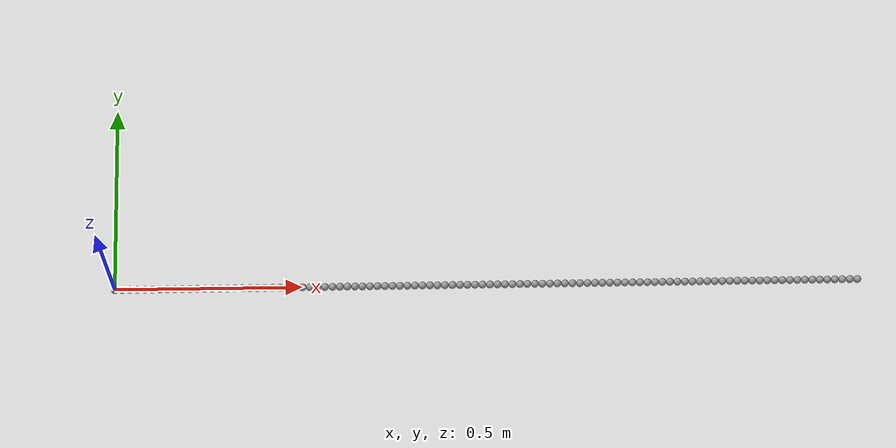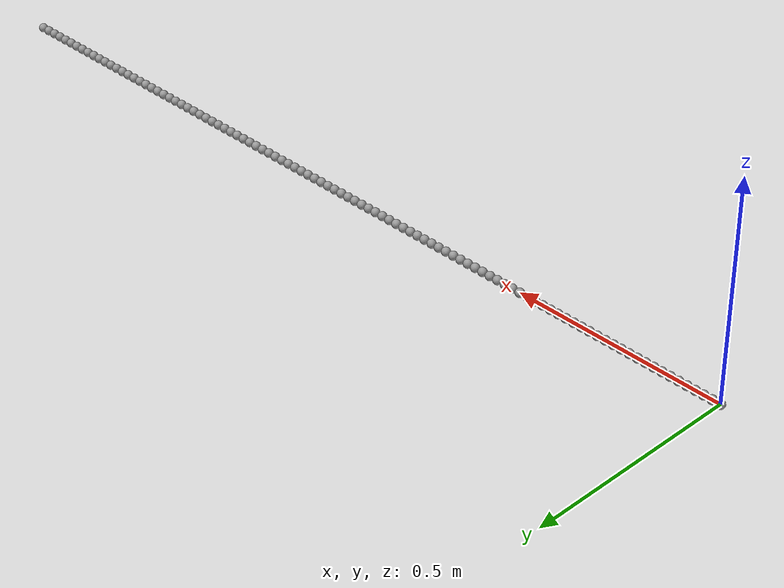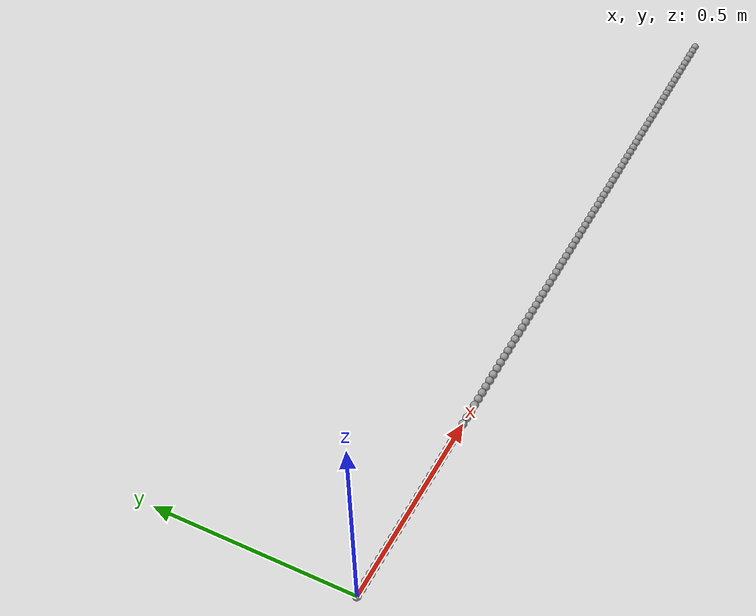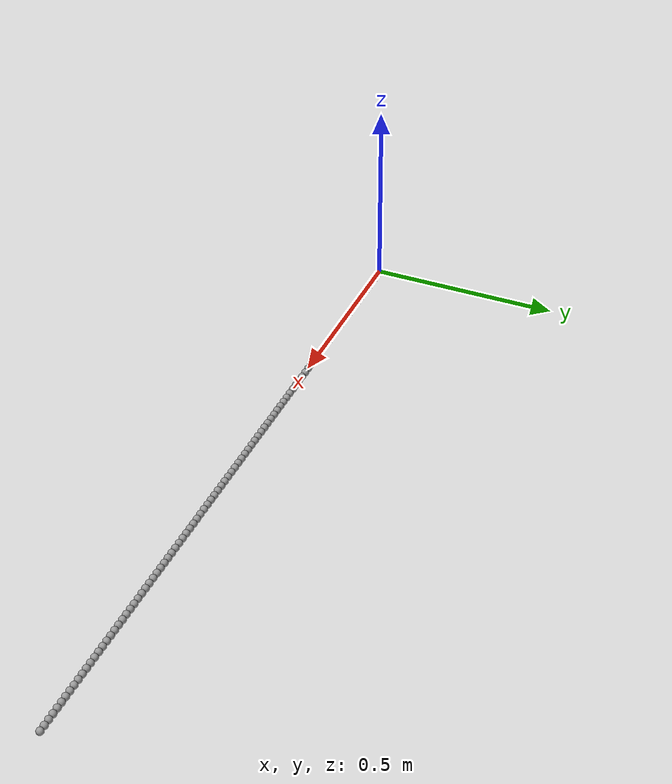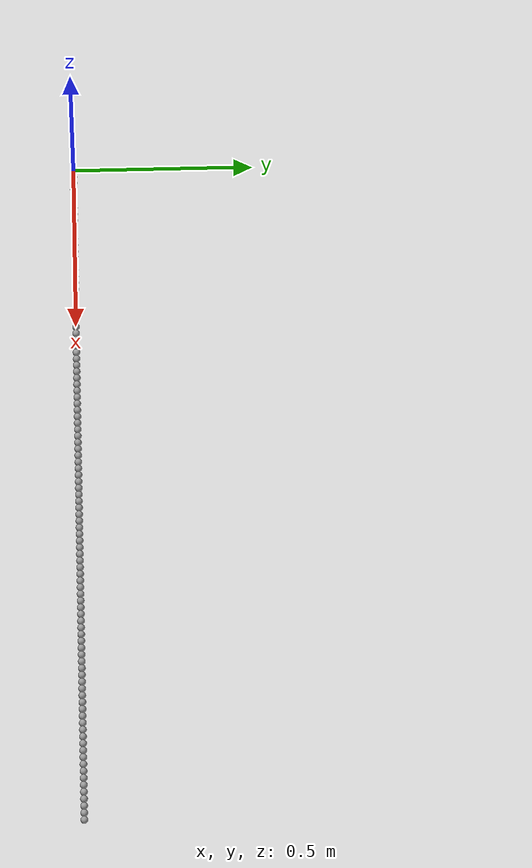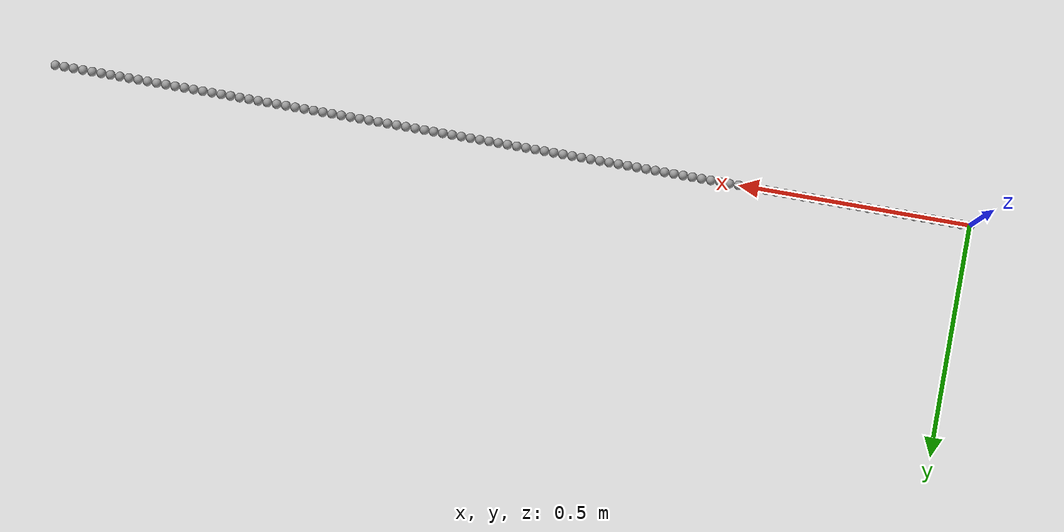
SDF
<?xml version='1.0'?>
 <sdf version='1.5'>
  <model name="tether_model">
   <static>false</static>

 				<!-- DEFINITION OF LINKS -->

    <link name='tether/sphere_01'>
      <pose>0 0 0 0 0 0</pose>

      <inertial>
        <mass>0.005000</mass>
        <inertia>
          <ixx>0.005000</ixx>
          <ixy>0.000000</ixy>
          <ixz>0.000000</ixz>
          <iyy>0.005000</iyy>
          <iyz>0.000000</iyz>
          <izz>0.005000</izz>
        </inertia>
      </inertial>
      <collision name="sphere_01_collision">
        <geometry>
          <sphere>
            <radius>0.0100</radius>
          </sphere>
        </geometry>
      </collision>
      <visual name="sphere_01_visual">
        <geometry>
          <sphere>
            <radius>0.0100</radius>
          </sphere>
        </geometry>
        <material>
          <script>
            <name>Gazebo/Grey</name>
          </script>
        </material>
      </visual>
    </link>

    <link name='tether/sphere_02'>
      <pose>0.02 0 0 0 0 0</pose>

      <inertial>
        <mass>0.005000</mass>
        <inertia>
          <ixx>0.005000</ixx>
          <ixy>0.000000</ixy>
          <ixz>0.000000</ixz>
          <iyy>0.005000</iyy>
          <iyz>0.000000</iyz>
          <izz>0.005000</izz>
        </inertia>
      </inertial>
      <collision name="sphere_02_collision">
        <geometry>
          <sphere>
            <radius>0.0100</radius>
          </sphere>
        </geometry>
      </collision>
      <visual name="sphere_02_visual">
        <geometry>
          <sphere>
            <radius>0.0100</radius>
          </sphere>
        </geometry>
        <material>
          <script>
            <name>Gazebo/Grey</name>
          </script>
        </material>
      </visual>
    </link>

    <joint name="tether/joint_01_02" type="revolute">
      <pose>-0.01 0 0 0 0 0</pose>
      <child>tether/sphere_02</child>
      <parent>tether/sphere_01</parent>
      <axis>
        <xyz>0.000000 1.000000 0.000000</xyz>
        <limit>
          <lower>-2.200000</lower>
          <upper>2.200000</upper>
        </limit>
        <dynamics>
          <damping>1.000000</damping>
        </dynamics>
      </axis>
    </joint>

    <link name='tether/sphere_03'>
      <pose>0.04 0 0 0 0 0</pose>

      <inertial>
        <mass>0.005000</mass>
        <inertia>
          <ixx>0.005000</ixx>
          <ixy>0.000000</ixy>
          <ixz>0.000000</ixz>
          <iyy>0.005000</iyy>
          <iyz>0.000000</iyz>
          <izz>0.005000</izz>
        </inertia>
      </inertial>
      <collision name="sphere_03_collision">
        <geometry>
          <sphere>
            <radius>0.0100</radius>
          </sphere>
        </geometry>
      </collision>
      <visual name="sphere_03_visual">
        <geometry>
          <sphere>
            <radius>0.0100</radius>
          </sphere>
        </geometry>
        <material>
          <script>
            <name>Gazebo/Grey</name>
          </script>
        </material>
      </visual>
    </link>

    <joint name="tether/joint_02_03" type="revolute">
      <pose>-0.01 0 0 0 0 0</pose>
      <child>tether/sphere_03</child>
      <parent>tether/sphere_02</parent>
      <axis>
        <xyz>0.000000 0.000000 1.000000</xyz>
        <limit>
          <lower>-2.200000</lower>
          <upper>2.200000</upper>
        </limit>
        <dynamics>
          <damping>1.000000</damping>
        </dynamics>
      </axis>
    </joint>

    <link name='tether/sphere_04'>
      <pose>0.06 0 0 0 0 0</pose>

      <inertial>
        <mass>0.005000</mass>
        <inertia>
          <ixx>0.005000</ixx>
          <ixy>0.000000</ixy>
          <ixz>0.000000</ixz>
          <iyy>0.005000</iyy>
          <iyz>0.000000</iyz>
          <izz>0.005000</izz>
        </inertia>
      </inertial>
      <collision name="sphere_04_collision">
        <geometry>
          <sphere>
            <radius>0.0100</radius>
          </sphere>
        </geometry>
      </collision>
      <visual name="sphere_04_visual">
        <geometry>
          <sphere>
            <radius>0.0100</radius>
          </sphere>
        </geometry>
        <material>
          <script>
            <name>Gazebo/Grey</name>
          </script>
        </material>
      </visual>
    </link>

    <joint name="tether/joint_03_04" type="revolute">
      <pose>-0.01 0 0 0 0 0</pose>
      <child>tether/sphere_04</child>
      <parent>tether/sphere_03</parent>
      <axis>
        <xyz>0.000000 1.000000 0.000000</xyz>
        <limit>
          <lower>-2.200000</lower>
          <upper>2.200000</upper>
        </limit>
        <dynamics>
          <damping>1.000000</damping>
        </dynamics>
      </axis>
    </joint>

    <link name='tether/sphere_05'>
      <pose>0.08 0 0 0 0 0</pose>

      <inertial>
        <mass>0.005000</mass>
        <inertia>
          <ixx>0.005000</ixx>
          <ixy>0.000000</ixy>
          <ixz>0.000000</ixz>
          <iyy>0.005000</iyy>
          <iyz>0.000000</iyz>
          <izz>0.005000</izz>
        </inertia>
      </inertial>
      <collision name="sphere_05_collision">
        <geometry>
          <sphere>
            <radius>0.0100</radius>
          </sphere>
        </geometry>
      </collision>
      <visual name="sphere_05_visual">
        <geometry>
          <sphere>
            <radius>0.0100</radius>
          </sphere>
        </geometry>
        <material>
          <script>
            <name>Gazebo/Grey</name>
          </script>
        </material>
      </visual>
    </link>

    <joint name="tether/joint_04_05" type="revolute">
      <pose>-0.01 0 0 0 0 0</pose>
      <child>tether/sphere_05</child>
      <parent>tether/sphere_04</parent>
      <axis>
        <xyz>0.000000 0.000000 1.000000</xyz>
        <limit>
          <lower>-2.200000</lower>
          <upper>2.200000</upper>
        </limit>
        <dynamics>
          <damping>1.000000</damping>
        </dynamics>
      </axis>
    </joint>

    <link name='tether/sphere_06'>
      <pose>0.1 0 0 0 0 0</pose>

      <inertial>
        <mass>0.005000</mass>
        <inertia>
          <ixx>0.005000</ixx>
          <ixy>0.000000</ixy>
          <ixz>0.000000</ixz>
          <iyy>0.005000</iyy>
          <iyz>0.000000</iyz>
          <izz>0.005000</izz>
        </inertia>
      </inertial>
      <collision name="sphere_06_collision">
        <geometry>
          <sphere>
            <radius>0.0100</radius>
          </sphere>
        </geometry>
      </collision>
      <visual name="sphere_06_visual">
        <geometry>
          <sphere>
            <radius>0.0100</radius>
          </sphere>
        </geometry>
        <material>
          <script>
            <name>Gazebo/Grey</name>
          </script>
        </material>
      </visual>
    </link>

    <joint name="tether/joint_05_06" type="revolute">
      <pose>-0.01 0 0 0 0 0</pose>
      <child>tether/sphere_06</child>
      <parent>tether/sphere_05</parent>
      <axis>
        <xyz>0.000000 1.000000 0.000000</xyz>
        <limit>
          <lower>-2.200000</lower>
          <upper>2.200000</upper>
        </limit>
        <dynamics>
          <damping>1.000000</damping>
        </dynamics>
      </axis>
    </joint>

    <link name='tether/sphere_07'>
      <pose>0.12 0 0 0 0 0</pose>

      <inertial>
        <mass>0.005000</mass>
        <inertia>
          <ixx>0.005000</ixx>
          <ixy>0.000000</ixy>
          <ixz>0.000000</ixz>
          <iyy>0.005000</iyy>
          <iyz>0.000000</iyz>
          <izz>0.005000</izz>
        </inertia>
      </inertial>
      <collision name="sphere_07_collision">
        <geometry>
          <sphere>
            <radius>0.0100</radius>
          </sphere>
        </geometry>
      </collision>
      <visual name="sphere_07_visual">
        <geometry>
          <sphere>
            <radius>0.0100</radius>
          </sphere>
        </geometry>
        <material>
          <script>
            <name>Gazebo/Grey</name>
          </script>
        </material>
      </visual>
    </link>

    <joint name="tether/joint_06_07" type="revolute">
      <pose>-0.01 0 0 0 0 0</pose>
      <child>tether/sphere_07</child>
      <parent>tether/sphere_06</parent>
      <axis>
        <xyz>0.000000 0.000000 1.000000</xyz>
        <limit>
          <lower>-2.200000</lower>
          <upper>2.200000</upper>
        </limit>
        <dynamics>
          <damping>1.000000</damping>
        </dynamics>
      </axis>
    </joint>

    <link name='tether/sphere_08'>
      <pose>0.14 0 0 0 0 0</pose>

      <inertial>
        <mass>0.005000</mass>
        <inertia>
          <ixx>0.005000</ixx>
          <ixy>0.000000</ixy>
          <ixz>0.000000</ixz>
          <iyy>0.005000</iyy>
          <iyz>0.000000</iyz>
          <izz>0.005000</izz>
        </inertia>
      </inertial>
      <collision name="sphere_08_collision">
        <geometry>
          <sphere>
            <radius>0.0100</radius>
          </sphere>
        </geometry>
      </collision>
      <visual name="sphere_08_visual">
        <geometry>
          <sphere>
            <radius>0.0100</radius>
          </sphere>
        </geometry>
        <material>
          <script>
            <name>Gazebo/Grey</name>
          </script>
        </material>
      </visual>
    </link>

    <joint name="tether/joint_07_08" type="revolute">
      <pose>-0.01 0 0 0 0 0</pose>
      <child>tether/sphere_08</child>
      <parent>tether/sphere_07</parent>
      <axis>
        <xyz>0.000000 1.000000 0.000000</xyz>
        <limit>
          <lower>-2.200000</lower>
          <upper>2.200000</upper>
        </limit>
        <dynamics>
          <damping>1.000000</damping>
        </dynamics>
      </axis>
    </joint>

    <link name='tether/sphere_09'>
      <pose>0.16 0 0 0 0 0</pose>

      <inertial>
        <mass>0.005000</mass>
        <inertia>
          <ixx>0.005000</ixx>
          <ixy>0.000000</ixy>
          <ixz>0.000000</ixz>
          <iyy>0.005000</iyy>
          <iyz>0.000000</iyz>
          <izz>0.005000</izz>
        </inertia>
      </inertial>
      <collision name="sphere_09_collision">
        <geometry>
          <sphere>
            <radius>0.0100</radius>
          </sphere>
        </geometry>
      </collision>
      <visual name="sphere_09_visual">
        <geometry>
          <sphere>
            <radius>0.0100</radius>
          </sphere>
        </geometry>
        <material>
          <script>
            <name>Gazebo/Grey</name>
          </script>
        </material>
      </visual>
    </link>

    <joint name="tether/joint_08_09" type="revolute">
      <pose>-0.01 0 0 0 0 0</pose>
      <child>tether/sphere_09</child>
      <parent>tether/sphere_08</parent>
      <axis>
        <xyz>0.000000 0.000000 1.000000</xyz>
        <limit>
          <lower>-2.200000</lower>
          <upper>2.200000</upper>
        </limit>
        <dynamics>
          <damping>1.000000</damping>
        </dynamics>
      </axis>
    </joint>

    <link name='tether/sphere_10'>
      <pose>0.18 0 0 0 0 0</pose>

      <inertial>
        <mass>0.005000</mass>
        <inertia>
          <ixx>0.005000</ixx>
          <ixy>0.000000</ixy>
          <ixz>0.000000</ixz>
          <iyy>0.005000</iyy>
          <iyz>0.000000</iyz>
          <izz>0.005000</izz>
        </inertia>
      </inertial>
      <collision name="sphere_10_collision">
        <geometry>
          <sphere>
            <radius>0.0100</radius>
          </sphere>
        </geometry>
      </collision>
      <visual name="sphere_10_visual">
        <geometry>
          <sphere>
            <radius>0.0100</radius>
          </sphere>
        </geometry>
        <material>
          <script>
            <name>Gazebo/Grey</name>
          </script>
        </material>
      </visual>
    </link>

    <joint name="tether/joint_09_10" type="revolute">
      <pose>-0.01 0 0 0 0 0</pose>
      <child>tether/sphere_10</child>
      <parent>tether/sphere_09</parent>
      <axis>
        <xyz>0.000000 1.000000 0.000000</xyz>
        <limit>
          <lower>-2.200000</lower>
          <upper>2.200000</upper>
        </limit>
        <dynamics>
          <damping>1.000000</damping>
        </dynamics>
      </axis>
    </joint>

    <link name='tether/sphere_11'>
      <pose>0.2 0 0 0 0 0</pose>

      <inertial>
        <mass>0.005000</mass>
        <inertia>
          <ixx>0.005000</ixx>
          <ixy>0.000000</ixy>
          <ixz>0.000000</ixz>
          <iyy>0.005000</iyy>
          <iyz>0.000000</iyz>
          <izz>0.005000</izz>
        </inertia>
      </inertial>
      <collision name="sphere_11_collision">
        <geometry>
          <sphere>
            <radius>0.0100</radius>
          </sphere>
        </geometry>
      </collision>
      <visual name="sphere_11_visual">
        <geometry>
          <sphere>
            <radius>0.0100</radius>
          </sphere>
        </geometry>
        <material>
          <script>
            <name>Gazebo/Grey</name>
          </script>
        </material>
      </visual>
    </link>

    <joint name="tether/joint_10_11" type="revolute">
      <pose>-0.01 0 0 0 0 0</pose>
      <child>tether/sphere_11</child>
      <parent>tether/sphere_10</parent>
      <axis>
        <xyz>0.000000 0.000000 1.000000</xyz>
        <limit>
          <lower>-2.200000</lower>
          <upper>2.200000</upper>
        </limit>
        <dynamics>
          <damping>1.000000</damping>
        </dynamics>
      </axis>
    </joint>

    <link name='tether/sphere_12'>
      <pose>0.22 0 0 0 0 0</pose>

      <inertial>
        <mass>0.005000</mass>
        <inertia>
          <ixx>0.005000</ixx>
          <ixy>0.000000</ixy>
          <ixz>0.000000</ixz>
          <iyy>0.005000</iyy>
          <iyz>0.000000</iyz>
          <izz>0.005000</izz>
        </inertia>
      </inertial>
      <collision name="sphere_12_collision">
        <geometry>
          <sphere>
            <radius>0.0100</radius>
          </sphere>
        </geometry>
      </collision>
      <visual name="sphere_12_visual">
        <geometry>
          <sphere>
            <radius>0.0100</radius>
          </sphere>
        </geometry>
        <material>
          <script>
            <name>Gazebo/Grey</name>
          </script>
        </material>
      </visual>
    </link>

    <joint name="tether/joint_11_12" type="revolute">
      <pose>-0.01 0 0 0 0 0</pose>
      <child>tether/sphere_12</child>
      <parent>tether/sphere_11</parent>
      <axis>
        <xyz>0.000000 1.000000 0.000000</xyz>
        <limit>
          <lower>-2.200000</lower>
          <upper>2.200000</upper>
        </limit>
        <dynamics>
          <damping>1.000000</damping>
        </dynamics>
      </axis>
    </joint>

    <link name='tether/sphere_13'>
      <pose>0.24 0 0 0 0 0</pose>

      <inertial>
        <mass>0.005000</mass>
        <inertia>
          <ixx>0.005000</ixx>
          <ixy>0.000000</ixy>
          <ixz>0.000000</ixz>
          <iyy>0.005000</iyy>
          <iyz>0.000000</iyz>
          <izz>0.005000</izz>
        </inertia>
      </inertial>
      <collision name="sphere_13_collision">
        <geometry>
          <sphere>
            <radius>0.0100</radius>
          </sphere>
        </geometry>
      </collision>
      <visual name="sphere_13_visual">
        <geometry>
          <sphere>
            <radius>0.0100</radius>
          </sphere>
        </geometry>
        <material>
          <script>
            <name>Gazebo/Grey</name>
          </script>
        </material>
      </visual>
    </link>

    <joint name="tether/joint_12_13" type="revolute">
      <pose>-0.01 0 0 0 0 0</pose>
      <child>tether/sphere_13</child>
      <parent>tether/sphere_12</parent>
      <axis>
        <xyz>0.000000 0.000000 1.000000</xyz>
        <limit>
          <lower>-2.200000</lower>
          <upper>2.200000</upper>
        </limit>
        <dynamics>
          <damping>1.000000</damping>
        </dynamics>
      </axis>
    </joint>

    <link name='tether/sphere_14'>
      <pose>0.26 0 0 0 0 0</pose>

      <inertial>
        <mass>0.005000</mass>
        <inertia>
          <ixx>0.005000</ixx>
          <ixy>0.000000</ixy>
          <ixz>0.000000</ixz>
          <iyy>0.005000</iyy>
          <iyz>0.000000</iyz>
          <izz>0.005000</izz>
        </inertia>
      </inertial>
      <collision name="sphere_14_collision">
        <geometry>
          <sphere>
            <radius>0.0100</radius>
          </sphere>
        </geometry>
      </collision>
      <visual name="sphere_14_visual">
        <geometry>
          <sphere>
            <radius>0.0100</radius>
          </sphere>
        </geometry>
        <material>
          <script>
            <name>Gazebo/Grey</name>
          </script>
        </material>
      </visual>
    </link>

    <joint name="tether/joint_13_14" type="revolute">
      <pose>-0.01 0 0 0 0 0</pose>
      <child>tether/sphere_14</child>
      <parent>tether/sphere_13</parent>
      <axis>
        <xyz>0.000000 1.000000 0.000000</xyz>
        <limit>
          <lower>-2.200000</lower>
          <upper>2.200000</upper>
        </limit>
        <dynamics>
          <damping>1.000000</damping>
        </dynamics>
      </axis>
    </joint>

    <link name='tether/sphere_15'>
      <pose>0.28 0 0 0 0 0</pose>

      <inertial>
        <mass>0.005000</mass>
        <inertia>
          <ixx>0.005000</ixx>
          <ixy>0.000000</ixy>
          <ixz>0.000000</ixz>
          <iyy>0.005000</iyy>
          <iyz>0.000000</iyz>
          <izz>0.005000</izz>
        </inertia>
      </inertial>
      <collision name="sphere_15_collision">
        <geometry>
          <sphere>
            <radius>0.0100</radius>
          </sphere>
        </geometry>
      </collision>
      <visual name="sphere_15_visual">
        <geometry>
          <sphere>
            <radius>0.0100</radius>
          </sphere>
        </geometry>
        <material>
          <script>
            <name>Gazebo/Grey</name>
          </script>
        </material>
      </visual>
    </link>

    <joint name="tether/joint_14_15" type="revolute">
      <pose>-0.01 0 0 0 0 0</pose>
      <child>tether/sphere_15</child>
      <parent>tether/sphere_14</parent>
      <axis>
        <xyz>0.000000 0.000000 1.000000</xyz>
        <limit>
          <lower>-2.200000</lower>
          <upper>2.200000</upper>
        </limit>
        <dynamics>
          <damping>1.000000</damping>
        </dynamics>
      </axis>
    </joint>

    <link name='tether/sphere_16'>
      <pose>0.30 0 0 0 0 0</pose>

      <inertial>
        <mass>0.005000</mass>
        <inertia>
          <ixx>0.005000</ixx>
          <ixy>0.000000</ixy>
          <ixz>0.000000</ixz>
          <iyy>0.005000</iyy>
          <iyz>0.000000</iyz>
          <izz>0.005000</izz>
        </inertia>
      </inertial>
      <collision name="sphere_16_collision">
        <geometry>
          <sphere>
            <radius>0.0100</radius>
          </sphere>
        </geometry>
      </collision>
      <visual name="sphere_16_visual">
        <geometry>
          <sphere>
            <radius>0.0100</radius>
          </sphere>
        </geometry>
        <material>
          <script>
            <name>Gazebo/Grey</name>
          </script>
        </material>
      </visual>
    </link>

    <joint name="tether/joint_15_16" type="revolute">
      <pose>-0.01 0 0 0 0 0</pose>
      <child>tether/sphere_16</child>
      <parent>tether/sphere_15</parent>
      <axis>
        <xyz>0.000000 1.000000 0.000000</xyz>
        <limit>
          <lower>-2.200000</lower>
          <upper>2.200000</upper>
        </limit>
        <dynamics>
          <damping>1.000000</damping>
        </dynamics>
      </axis>
    </joint>

    <link name='tether/sphere_17'>
      <pose>0.32 0 0 0 0 0</pose>

      <inertial>
        <mass>0.005000</mass>
        <inertia>
          <ixx>0.005000</ixx>
          <ixy>0.000000</ixy>
          <ixz>0.000000</ixz>
          <iyy>0.005000</iyy>
          <iyz>0.000000</iyz>
          <izz>0.005000</izz>
        </inertia>
      </inertial>
      <collision name="sphere_17_collision">
        <geometry>
          <sphere>
            <radius>0.0100</radius>
          </sphere>
        </geometry>
      </collision>
      <visual name="sphere_17_visual">
        <geometry>
          <sphere>
            <radius>0.0100</radius>
          </sphere>
        </geometry>
        <material>
          <script>
            <name>Gazebo/Grey</name>
          </script>
        </material>
      </visual>
    </link>

    <joint name="tether/joint_16_17" type="revolute">
      <pose>-0.01 0 0 0 0 0</pose>
      <child>tether/sphere_17</child>
      <parent>tether/sphere_16</parent>
      <axis>
        <xyz>0.000000 0.000000 1.000000</xyz>
        <limit>
          <lower>-2.200000</lower>
          <upper>2.200000</upper>
        </limit>
        <dynamics>
          <damping>1.000000</damping>
        </dynamics>
      </axis>
    </joint>

    <link name='tether/sphere_18'>
      <pose>0.34 0 0 0 0 0</pose>

      <inertial>
        <mass>0.005000</mass>
        <inertia>
          <ixx>0.005000</ixx>
          <ixy>0.000000</ixy>
          <ixz>0.000000</ixz>
          <iyy>0.005000</iyy>
          <iyz>0.000000</iyz>
          <izz>0.005000</izz>
        </inertia>
      </inertial>
      <collision name="sphere_18_collision">
        <geometry>
          <sphere>
            <radius>0.0100</radius>
          </sphere>
        </geometry>
      </collision>
      <visual name="sphere_18_visual">
        <geometry>
          <sphere>
            <radius>0.0100</radius>
          </sphere>
        </geometry>
        <material>
          <script>
            <name>Gazebo/Grey</name>
          </script>
        </material>
      </visual>
    </link>

    <joint name="tether/joint_17_18" type="revolute">
      <pose>-0.01 0 0 0 0 0</pose>
      <child>tether/sphere_18</child>
      <parent>tether/sphere_17</parent>
      <axis>
        <xyz>0.000000 1.000000 0.000000</xyz>
        <limit>
          <lower>-2.200000</lower>
          <upper>2.200000</upper>
        </limit>
        <dynamics>
          <damping>1.000000</damping>
        </dynamics>
      </axis>
    </joint>

    <link name='tether/sphere_19'>
      <pose>0.36 0 0 0 0 0</pose>

      <inertial>
        <mass>0.005000</mass>
        <inertia>
          <ixx>0.005000</ixx>
          <ixy>0.000000</ixy>
          <ixz>0.000000</ixz>
          <iyy>0.005000</iyy>
          <iyz>0.000000</iyz>
          <izz>0.005000</izz>
        </inertia>
      </inertial>
      <collision name="sphere_19_collision">
        <geometry>
          <sphere>
            <radius>0.0100</radius>
          </sphere>
        </geometry>
      </collision>
      <visual name="sphere_19_visual">
        <geometry>
          <sphere>
            <radius>0.0100</radius>
          </sphere>
        </geometry>
        <material>
          <script>
            <name>Gazebo/Grey</name>
          </script>
        </material>
      </visual>
    </link>

    <joint name="tether/joint_18_19" type="revolute">
      <pose>-0.01 0 0 0 0 0</pose>
      <child>tether/sphere_19</child>
      <parent>tether/sphere_18</parent>
      <axis>
        <xyz>0.000000 0.000000 1.000000</xyz>
        <limit>
          <lower>-2.200000</lower>
          <upper>2.200000</upper>
        </limit>
        <dynamics>
          <damping>1.000000</damping>
        </dynamics>
      </axis>
    </joint>

    <link name='tether/sphere_20'>
      <pose>0.38 0 0 0 0 0</pose>

      <inertial>
        <mass>0.005000</mass>
        <inertia>
          <ixx>0.005000</ixx>
          <ixy>0.000000</ixy>
          <ixz>0.000000</ixz>
          <iyy>0.005000</iyy>
          <iyz>0.000000</iyz>
          <izz>0.005000</izz>
        </inertia>
      </inertial>
      <collision name="sphere_20_collision">
        <geometry>
          <sphere>
            <radius>0.0100</radius>
          </sphere>
        </geometry>
      </collision>
      <visual name="sphere_20_visual">
        <geometry>
          <sphere>
            <radius>0.0100</radius>
          </sphere>
        </geometry>
        <material>
          <script>
            <name>Gazebo/Grey</name>
          </script>
        </material>
      </visual>
    </link>

    <joint name="tether/joint_19_20" type="revolute">
      <pose>-0.01 0 0 0 0 0</pose>
      <child>tether/sphere_20</child>
      <parent>tether/sphere_19</parent>
      <axis>
        <xyz>0.000000 1.000000 0.000000</xyz>
        <limit>
          <lower>-2.200000</lower>
          <upper>2.200000</upper>
        </limit>
        <dynamics>
          <damping>1.000000</damping>
        </dynamics>
      </axis>
    </joint>

    <link name='tether/sphere_21'>
      <pose>0.40 0 0 0 0 0</pose>

      <inertial>
        <mass>0.005000</mass>
        <inertia>
          <ixx>0.005000</ixx>
          <ixy>0.000000</ixy>
          <ixz>0.000000</ixz>
          <iyy>0.005000</iyy>
          <iyz>0.000000</iyz>
          <izz>0.005000</izz>
        </inertia>
      </inertial>
      <collision name="sphere_21_collision">
        <geometry>
          <sphere>
            <radius>0.0100</radius>
          </sphere>
        </geometry>
      </collision>
      <visual name="sphere_21_visual">
        <geometry>
          <sphere>
            <radius>0.0100</radius>
          </sphere>
        </geometry>
        <material>
          <script>
            <name>Gazebo/Grey</name>
          </script>
        </material>
      </visual>
    </link>

    <joint name="tether/joint_20_21" type="revolute">
      <pose>-0.01 0 0 0 0 0</pose>
      <child>tether/sphere_21</child>
      <parent>tether/sphere_20</parent>
      <axis>
        <xyz>0.000000 1.000000 0.000000</xyz>
        <limit>
          <lower>-2.200000</lower>
          <upper>2.200000</upper>
        </limit>
        <dynamics>
          <damping>1.000000</damping>
        </dynamics>
      </axis>
    </joint>

    <link name='tether/sphere_22'>
      <pose>0.42 0 0 0 0 0</pose>

      <inertial>
        <mass>0.005000</mass>
        <inertia>
          <ixx>0.005000</ixx>
          <ixy>0.000000</ixy>
          <ixz>0.000000</ixz>
          <iyy>0.005000</iyy>
          <iyz>0.000000</iyz>
          <izz>0.005000</izz>
        </inertia>
      </inertial>
      <collision name="sphere_22_collision">
        <geometry>
          <sphere>
            <radius>0.0100</radius>
          </sphere>
        </geometry>
      </collision>
      <visual name="sphere_22_visual">
        <geometry>
          <sphere>
            <radius>0.0100</radius>
          </sphere>
        </geometry>
        <material>
          <script>
            <name>Gazebo/Grey</name>
          </script>
        </material>
      </visual>
    </link>

    <joint name="tether/joint_21_22" type="revolute">
      <pose>-0.01 0 0 0 0 0</pose>
      <child>tether/sphere_22</child>
      <parent>tether/sphere_21</parent>
      <axis>
        <xyz>0.000000 1.000000 0.000000</xyz>
        <limit>
          <lower>-2.200000</lower>
          <upper>2.200000</upper>
        </limit>
        <dynamics>
          <damping>1.000000</damping>
        </dynamics>
      </axis>
    </joint>

    <link name='tether/sphere_23'>
      <pose>0.44 0 0 0 0 0</pose>

      <inertial>
        <mass>0.005000</mass>
        <inertia>
          <ixx>0.005000</ixx>
          <ixy>0.000000</ixy>
          <ixz>0.000000</ixz>
          <iyy>0.005000</iyy>
          <iyz>0.000000</iyz>
          <izz>0.005000</izz>
        </inertia>
      </inertial>
      <collision name="sphere_23_collision">
        <geometry>
          <sphere>
            <radius>0.0100</radius>
          </sphere>
        </geometry>
      </collision>
      <visual name="sphere_23_visual">
        <geometry>
          <sphere>
            <radius>0.0100</radius>
          </sphere>
        </geometry>
        <material>
          <script>
            <name>Gazebo/Grey</name>
          </script>
        </material>
      </visual>
    </link>

    <joint name="tether/joint_22_23" type="revolute">
      <pose>-0.01 0 0 0 0 0</pose>
      <child>tether/sphere_23</child>
      <parent>tether/sphere_22</parent>
      <axis>
        <xyz>0.000000 0.000000 1.000000</xyz>
        <limit>
          <lower>-2.200000</lower>
          <upper>2.200000</upper>
        </limit>
        <dynamics>
          <damping>1.000000</damping>
        </dynamics>
      </axis>
    </joint>

    <link name='tether/sphere_24'>
      <pose>0.46 0 0 0 0 0</pose>

      <inertial>
        <mass>0.005000</mass>
        <inertia>
          <ixx>0.005000</ixx>
          <ixy>0.000000</ixy>
          <ixz>0.000000</ixz>
          <iyy>0.005000</iyy>
          <iyz>0.000000</iyz>
          <izz>0.005000</izz>
        </inertia>
      </inertial>
      <collision name="sphere_24_collision">
        <geometry>
          <sphere>
            <radius>0.0100</radius>
          </sphere>
        </geometry>
      </collision>
      <visual name="sphere_24_visual">
        <geometry>
          <sphere>
            <radius>0.0100</radius>
          </sphere>
        </geometry>
        <material>
          <script>
            <name>Gazebo/Grey</name>
          </script>
        </material>
      </visual>
    </link>

    <joint name="tether/joint_23_24" type="revolute">
      <pose>-0.01 0 0 0 0 0</pose>
      <child>tether/sphere_24</child>
      <parent>tether/sphere_23</parent>
      <axis>
        <xyz>0.000000 1.000000 0.000000</xyz>
        <limit>
          <lower>-2.200000</lower>
          <upper>2.200000</upper>
        </limit>
        <dynamics>
          <damping>1.000000</damping>
        </dynamics>
      </axis>
    </joint>

    <link name='tether/sphere_25'>
      <pose>0.48 0 0 0 0 0</pose>

      <inertial>
        <mass>0.005000</mass>
        <inertia>
          <ixx>0.005000</ixx>
          <ixy>0.000000</ixy>
          <ixz>0.000000</ixz>
          <iyy>0.005000</iyy>
          <iyz>0.000000</iyz>
          <izz>0.005000</izz>
        </inertia>
      </inertial>
      <collision name="sphere_25_collision">
        <geometry>
          <sphere>
            <radius>0.0100</radius>
          </sphere>
        </geometry>
      </collision>
      <visual name="sphere_25_visual">
        <geometry>
          <sphere>
            <radius>0.0100</radius>
          </sphere>
        </geometry>
        <material>
          <script>
            <name>Gazebo/Grey</name>
          </script>
        </material>
      </visual>
    </link>

    <joint name="tether/joint_24_25" type="revolute">
      <pose>-0.01 0 0 0 0 0</pose>
      <child>tether/sphere_25</child>
      <parent>tether/sphere_24</parent>
      <axis>
        <xyz>0.000000 0.000000 1.000000</xyz>
        <limit>
          <lower>-2.200000</lower>
          <upper>2.200000</upper>
        </limit>
        <dynamics>
          <damping>1.000000</damping>
        </dynamics>
      </axis>
    </joint>

    <link name='tether/sphere_26'>
      <pose>0.50 0 0 0 0 0</pose>

      <inertial>
        <mass>0.005000</mass>
        <inertia>
          <ixx>0.005000</ixx>
          <ixy>0.000000</ixy>
          <ixz>0.000000</ixz>
          <iyy>0.005000</iyy>
          <iyz>0.000000</iyz>
          <izz>0.005000</izz>
        </inertia>
      </inertial>
      <collision name="sphere_26_collision">
        <geometry>
          <sphere>
            <radius>0.0100</radius>
          </sphere>
        </geometry>
      </collision>
      <visual name="sphere_26_visual">
        <geometry>
          <sphere>
            <radius>0.0100</radius>
          </sphere>
        </geometry>
        <material>
          <script>
            <name>Gazebo/Grey</name>
          </script>
        </material>
      </visual>
    </link>

    <joint name="tether/joint_25_26" type="revolute">
      <pose>-0.01 0 0 0 0 0</pose>
      <child>tether/sphere_26</child>
      <parent>tether/sphere_25</parent>
      <axis>
        <xyz>0.000000 1.000000 0.000000</xyz>
        <limit>
          <lower>-2.200000</lower>
          <upper>2.200000</upper>
        </limit>
        <dynamics>
          <damping>1.000000</damping>
        </dynamics>
      </axis>
    </joint>

    <link name='tether/sphere_27'>
      <pose>0.52 0 0 0 0 0</pose>

      <inertial>
        <mass>0.005000</mass>
        <inertia>
          <ixx>0.005000</ixx>
          <ixy>0.000000</ixy>
          <ixz>0.000000</ixz>
          <iyy>0.005000</iyy>
          <iyz>0.000000</iyz>
          <izz>0.005000</izz>
        </inertia>
      </inertial>
      <collision name="sphere_27_collision">
        <geometry>
          <sphere>
            <radius>0.0100</radius>
          </sphere>
        </geometry>
      </collision>
      <visual name="sphere_27_visual">
        <geometry>
          <sphere>
            <radius>0.0100</radius>
          </sphere>
        </geometry>
        <material>
          <script>
            <name>Gazebo/Grey</name>
          </script>
        </material>
      </visual>
    </link>

    <joint name="tether/joint_26_27" type="revolute">
      <pose>-0.01 0 0 0 0 0</pose>
      <child>tether/sphere_27</child>
      <parent>tether/sphere_26</parent>
      <axis>
        <xyz>0.000000 0.000000 1.000000</xyz>
        <limit>
          <lower>-2.200000</lower>
          <upper>2.200000</upper>
        </limit>
        <dynamics>
          <damping>1.000000</damping>
        </dynamics>
      </axis>
    </joint>

    <link name='tether/sphere_28'>
      <pose>0.54 0 0 0 0 0</pose>

      <inertial>
        <mass>0.005000</mass>
        <inertia>
          <ixx>0.005000</ixx>
          <ixy>0.000000</ixy>
          <ixz>0.000000</ixz>
          <iyy>0.005000</iyy>
          <iyz>0.000000</iyz>
          <izz>0.005000</izz>
        </inertia>
      </inertial>
      <collision name="sphere_08_collision">
        <geometry>
          <sphere>
            <radius>0.0100</radius>
          </sphere>
        </geometry>
      </collision>
      <visual name="sphere_08_visual">
        <geometry>
          <sphere>
            <radius>0.0100</radius>
          </sphere>
        </geometry>
        <material>
          <script>
            <name>Gazebo/Grey</name>
          </script>
        </material>
      </visual>
    </link>

    <joint name="tether/joint_27_28" type="revolute">
      <pose>-0.01 0 0 0 0 0</pose>
      <child>tether/sphere_28</child>
      <parent>tether/sphere_27</parent>
      <axis>
        <xyz>0.000000 1.000000 0.000000</xyz>
        <limit>
          <lower>-2.200000</lower>
          <upper>2.200000</upper>
        </limit>
        <dynamics>
          <damping>1.000000</damping>
        </dynamics>
      </axis>
    </joint>

    <link name='tether/sphere_29'>
      <pose>0.56 0 0 0 0 0</pose>

      <inertial>
        <mass>0.005000</mass>
        <inertia>
          <ixx>0.005000</ixx>
          <ixy>0.000000</ixy>
          <ixz>0.000000</ixz>
          <iyy>0.005000</iyy>
          <iyz>0.000000</iyz>
          <izz>0.005000</izz>
        </inertia>
      </inertial>
      <collision name="sphere_29_collision">
        <geometry>
          <sphere>
            <radius>0.0100</radius>
          </sphere>
        </geometry>
      </collision>
      <visual name="sphere_29_visual">
        <geometry>
          <sphere>
            <radius>0.0100</radius>
          </sphere>
        </geometry>
        <material>
          <script>
            <name>Gazebo/Grey</name>
          </script>
        </material>
      </visual>
    </link>

    <joint name="tether/joint_28_29" type="revolute">
      <pose>-0.01 0 0 0 0 0</pose>
      <child>tether/sphere_29</child>
      <parent>tether/sphere_28</parent>
      <axis>
        <xyz>0.000000 0.000000 1.000000</xyz>
        <limit>
          <lower>-2.200000</lower>
          <upper>2.200000</upper>
        </limit>
        <dynamics>
          <damping>1.000000</damping>
        </dynamics>
      </axis>
    </joint>

    <link name='tether/sphere_30'>
      <pose>0.58 0 0 0 0 0</pose>

      <inertial>
        <mass>0.005000</mass>
        <inertia>
          <ixx>0.005000</ixx>
          <ixy>0.000000</ixy>
          <ixz>0.000000</ixz>
          <iyy>0.005000</iyy>
          <iyz>0.000000</iyz>
          <izz>0.005000</izz>
        </inertia>
      </inertial>
      <collision name="sphere_30_collision">
        <geometry>
          <sphere>
            <radius>0.0100</radius>
          </sphere>
        </geometry>
      </collision>
      <visual name="sphere_30_visual">
        <geometry>
          <sphere>
            <radius>0.0100</radius>
          </sphere>
        </geometry>
        <material>
          <script>
            <name>Gazebo/Grey</name>
          </script>
        </material>
      </visual>
    </link>

    <joint name="tether/joint_29_30" type="revolute">
      <pose>-0.01 0 0 0 0 0</pose>
      <child>tether/sphere_30</child>
      <parent>tether/sphere_29</parent>
      <axis>
        <xyz>0.000000 1.000000 0.000000</xyz>
        <limit>
          <lower>-2.200000</lower>
          <upper>2.200000</upper>
        </limit>
        <dynamics>
          <damping>1.000000</damping>
        </dynamics>
      </axis>
    </joint>

    <link name='tether/sphere_31'>
      <pose>0.60 0 0 0 0 0</pose>

      <inertial>
        <mass>0.005000</mass>
        <inertia>
          <ixx>0.005000</ixx>
          <ixy>0.000000</ixy>
          <ixz>0.000000</ixz>
          <iyy>0.005000</iyy>
          <iyz>0.000000</iyz>
          <izz>0.005000</izz>
        </inertia>
      </inertial>
      <collision name="sphere_31_collision">
        <geometry>
          <sphere>
            <radius>0.0100</radius>
          </sphere>
        </geometry>
      </collision>
      <visual name="sphere_31_visual">
        <geometry>
          <sphere>
            <radius>0.0100</radius>
          </sphere>
        </geometry>
        <material>
          <script>
            <name>Gazebo/Grey</name>
          </script>
        </material>
      </visual>
    </link>

    <joint name="tether/joint_30_31" type="revolute">
      <pose>-0.01 0 0 0 0 0</pose>
      <child>tether/sphere_31</child>
      <parent>tether/sphere_30</parent>
      <axis>
        <xyz>0.000000 0.000000 1.000000</xyz>
        <limit>
          <lower>-2.200000</lower>
          <upper>2.200000</upper>
        </limit>
        <dynamics>
          <damping>1.000000</damping>
        </dynamics>
      </axis>
    </joint>

    <link name='tether/sphere_32'>
      <pose>0.62 0 0 0 0 0</pose>

      <inertial>
        <mass>0.005000</mass>
        <inertia>
          <ixx>0.005000</ixx>
          <ixy>0.000000</ixy>
          <ixz>0.000000</ixz>
          <iyy>0.005000</iyy>
          <iyz>0.000000</iyz>
          <izz>0.005000</izz>
        </inertia>
      </inertial>
      <collision name="sphere_32_collision">
        <geometry>
          <sphere>
            <radius>0.0100</radius>
          </sphere>
        </geometry>
      </collision>
      <visual name="sphere_32_visual">
        <geometry>
          <sphere>
            <radius>0.0100</radius>
          </sphere>
        </geometry>
        <material>
          <script>
            <name>Gazebo/Grey</name>
          </script>
        </material>
      </visual>
    </link>

    <joint name="tether/joint_31_32" type="revolute">
      <pose>-0.01 0 0 0 0 0</pose>
      <child>tether/sphere_32</child>
      <parent>tether/sphere_31</parent>
      <axis>
        <xyz>0.000000 1.000000 0.000000</xyz>
        <limit>
          <lower>-2.200000</lower>
          <upper>2.200000</upper>
        </limit>
        <dynamics>
          <damping>1.000000</damping>
        </dynamics>
      </axis>
    </joint>

    <link name='tether/sphere_33'>
      <pose>0.64 0 0 0 0 0</pose>

      <inertial>
        <mass>0.005000</mass>
        <inertia>
          <ixx>0.005000</ixx>
          <ixy>0.000000</ixy>
          <ixz>0.000000</ixz>
          <iyy>0.005000</iyy>
          <iyz>0.000000</iyz>
          <izz>0.005000</izz>
        </inertia>
      </inertial>
      <collision name="sphere_33_collision">
        <geometry>
          <sphere>
            <radius>0.0100</radius>
          </sphere>
        </geometry>
      </collision>
      <visual name="sphere_33_visual">
        <geometry>
          <sphere>
            <radius>0.0100</radius>
          </sphere>
        </geometry>
        <material>
          <script>
            <name>Gazebo/Grey</name>
          </script>
        </material>
      </visual>
    </link>

    <joint name="tether/joint_32_33" type="revolute">
      <pose>-0.01 0 0 0 0 0</pose>
      <child>tether/sphere_33</child>
      <parent>tether/sphere_32</parent>
      <axis>
        <xyz>0.000000 0.000000 1.000000</xyz>
        <limit>
          <lower>-2.200000</lower>
          <upper>2.200000</upper>
        </limit>
        <dynamics>
          <damping>1.000000</damping>
        </dynamics>
      </axis>
    </joint>

    <link name='tether/sphere_34'>
      <pose>0.66 0 0 0 0 0</pose>

      <inertial>
        <mass>0.005000</mass>
        <inertia>
          <ixx>0.005000</ixx>
          <ixy>0.000000</ixy>
          <ixz>0.000000</ixz>
          <iyy>0.005000</iyy>
          <iyz>0.000000</iyz>
          <izz>0.005000</izz>
        </inertia>
      </inertial>
      <collision name="sphere_34_collision">
        <geometry>
          <sphere>
            <radius>0.0100</radius>
          </sphere>
        </geometry>
      </collision>
      <visual name="sphere_34_visual">
        <geometry>
          <sphere>
            <radius>0.0100</radius>
          </sphere>
        </geometry>
        <material>
          <script>
            <name>Gazebo/Grey</name>
          </script>
        </material>
      </visual>
    </link>

    <joint name="tether/joint_33_34" type="revolute">
      <pose>-0.01 0 0 0 0 0</pose>
      <child>tether/sphere_34</child>
      <parent>tether/sphere_33</parent>
      <axis>
        <xyz>0.000000 1.000000 0.000000</xyz>
        <limit>
          <lower>-2.200000</lower>
          <upper>2.200000</upper>
        </limit>
        <dynamics>
          <damping>1.000000</damping>
        </dynamics>
      </axis>
    </joint>

    <link name='tether/sphere_35'>
      <pose>0.68 0 0 0 0 0</pose>

      <inertial>
        <mass>0.005000</mass>
        <inertia>
          <ixx>0.005000</ixx>
          <ixy>0.000000</ixy>
          <ixz>0.000000</ixz>
          <iyy>0.005000</iyy>
          <iyz>0.000000</iyz>
          <izz>0.005000</izz>
        </inertia>
      </inertial>
      <collision name="sphere_35_collision">
        <geometry>
          <sphere>
            <radius>0.0100</radius>
          </sphere>
        </geometry>
      </collision>
      <visual name="sphere_35_visual">
        <geometry>
          <sphere>
            <radius>0.0100</radius>
          </sphere>
        </geometry>
        <material>
          <script>
            <name>Gazebo/Grey</name>
          </script>
        </material>
      </visual>
    </link>

    <joint name="tether/joint_34_35" type="revolute">
      <pose>-0.01 0 0 0 0 0</pose>
      <child>tether/sphere_35</child>
      <parent>tether/sphere_34</parent>
      <axis>
        <xyz>0.000000 0.000000 1.000000</xyz>
        <limit>
          <lower>-2.200000</lower>
          <upper>2.200000</upper>
        </limit>
        <dynamics>
          <damping>1.000000</damping>
        </dynamics>
      </axis>
    </joint>

    <link name='tether/sphere_36'>
      <pose>0.70 0 0 0 0 0</pose>

      <inertial>
        <mass>0.005000</mass>
        <inertia>
          <ixx>0.005000</ixx>
          <ixy>0.000000</ixy>
          <ixz>0.000000</ixz>
          <iyy>0.005000</iyy>
          <iyz>0.000000</iyz>
          <izz>0.005000</izz>
        </inertia>
      </inertial>
      <collision name="sphere_36_collision">
        <geometry>
          <sphere>
            <radius>0.0100</radius>
          </sphere>
        </geometry>
      </collision>
      <visual name="sphere_36_visual">
        <geometry>
          <sphere>
            <radius>0.0100</radius>
          </sphere>
        </geometry>
        <material>
          <script>
            <name>Gazebo/Grey</name>
          </script>
        </material>
      </visual>
    </link>

    <joint name="tether/joint_35_36" type="revolute">
      <pose>-0.01 0 0 0 0 0</pose>
      <child>tether/sphere_36</child>
      <parent>tether/sphere_35</parent>
      <axis>
        <xyz>0.000000 1.000000 0.000000</xyz>
        <limit>
          <lower>-2.200000</lower>
          <upper>2.200000</upper>
        </limit>
        <dynamics>
          <damping>1.000000</damping>
        </dynamics>
      </axis>
    </joint>

    <link name='tether/sphere_37'>
      <pose>0.72 0 0 0 0 0</pose>

      <inertial>
        <mass>0.005000</mass>
        <inertia>
          <ixx>0.005000</ixx>
          <ixy>0.000000</ixy>
          <ixz>0.000000</ixz>
          <iyy>0.005000</iyy>
          <iyz>0.000000</iyz>
          <izz>0.005000</izz>
        </inertia>
      </inertial>
      <collision name="sphere_37_collision">
        <geometry>
          <sphere>
            <radius>0.0100</radius>
          </sphere>
        </geometry>
      </collision>
      <visual name="sphere_37_visual">
        <geometry>
          <sphere>
            <radius>0.0100</radius>
          </sphere>
        </geometry>
        <material>
          <script>
            <name>Gazebo/Grey</name>
          </script>
        </material>
      </visual>
    </link>

    <joint name="tether/joint_36_37" type="revolute">
      <pose>-0.01 0 0 0 0 0</pose>
      <child>tether/sphere_37</child>
      <parent>tether/sphere_36</parent>
      <axis>
        <xyz>0.000000 0.000000 1.000000</xyz>
        <limit>
          <lower>-2.200000</lower>
          <upper>2.200000</upper>
        </limit>
        <dynamics>
          <damping>1.000000</damping>
        </dynamics>
      </axis>
    </joint>

    <link name='tether/sphere_38'>
      <pose>0.74 0 0 0 0 0</pose>

      <inertial>
        <mass>0.005000</mass>
        <inertia>
          <ixx>0.005000</ixx>
          <ixy>0.000000</ixy>
          <ixz>0.000000</ixz>
          <iyy>0.005000</iyy>
          <iyz>0.000000</iyz>
          <izz>0.005000</izz>
        </inertia>
      </inertial>
      <collision name="sphere_38_collision">
        <geometry>
          <sphere>
            <radius>0.0100</radius>
          </sphere>
        </geometry>
      </collision>
      <visual name="sphere_38_visual">
        <geometry>
          <sphere>
            <radius>0.0100</radius>
          </sphere>
        </geometry>
        <material>
          <script>
            <name>Gazebo/Grey</name>
          </script>
        </material>
      </visual>
    </link>

    <joint name="tether/joint_37_38" type="revolute">
      <pose>-0.01 0 0 0 0 0</pose>
      <child>tether/sphere_38</child>
      <parent>tether/sphere_37</parent>
      <axis>
        <xyz>0.000000 1.000000 0.000000</xyz>
        <limit>
          <lower>-2.200000</lower>
          <upper>2.200000</upper>
        </limit>
        <dynamics>
          <damping>1.000000</damping>
        </dynamics>
      </axis>
    </joint>

    <link name='tether/sphere_39'>
      <pose>0.76 0 0 0 0 0</pose>

      <inertial>
        <mass>0.005000</mass>
        <inertia>
          <ixx>0.005000</ixx>
          <ixy>0.000000</ixy>
          <ixz>0.000000</ixz>
          <iyy>0.005000</iyy>
          <iyz>0.000000</iyz>
          <izz>0.005000</izz>
        </inertia>
      </inertial>
      <collision name="sphere_39_collision">
        <geometry>
          <sphere>
            <radius>0.0100</radius>
          </sphere>
        </geometry>
      </collision>
      <visual name="sphere_39_visual">
        <geometry>
          <sphere>
            <radius>0.0100</radius>
          </sphere>
        </geometry>
        <material>
          <script>
            <name>Gazebo/Grey</name>
          </script>
        </material>
      </visual>
    </link>

    <joint name="tether/joint_38_39" type="revolute">
      <pose>-0.01 0 0 0 0 0</pose>
      <child>tether/sphere_39</child>
      <parent>tether/sphere_38</parent>
      <axis>
        <xyz>0.000000 0.000000 1.000000</xyz>
        <limit>
          <lower>-2.200000</lower>
          <upper>2.200000</upper>
        </limit>
        <dynamics>
          <damping>1.000000</damping>
        </dynamics>
      </axis>
    </joint>

    <link name='tether/sphere_40'>
      <pose>0.78 0 0 0 0 0</pose>

      <inertial>
        <mass>0.005000</mass>
        <inertia>
          <ixx>0.005000</ixx>
          <ixy>0.000000</ixy>
          <ixz>0.000000</ixz>
          <iyy>0.005000</iyy>
          <iyz>0.000000</iyz>
          <izz>0.005000</izz>
        </inertia>
      </inertial>
      <collision name="sphere_40_collision">
        <geometry>
          <sphere>
            <radius>0.0100</radius>
          </sphere>
        </geometry>
      </collision>
      <visual name="sphere_40_visual">
        <geometry>
          <sphere>
            <radius>0.0100</radius>
          </sphere>
        </geometry>
        <material>
          <script>
            <name>Gazebo/Grey</name>
          </script>
        </material>
      </visual>
    </link>

    <joint name="tether/joint_39_40" type="revolute">
      <pose>-0.01 0 0 0 0 0</pose>
      <child>tether/sphere_40</child>
      <parent>tether/sphere_39</parent>
      <axis>
        <xyz>0.000000 1.000000 0.000000</xyz>
        <limit>
          <lower>-2.200000</lower>
          <upper>2.200000</upper>
        </limit>
        <dynamics>
          <damping>1.000000</damping>
        </dynamics>
      </axis>
    </joint>

        <link name='tether/sphere_41'>
      <pose>0.80 0 0 0 0 0</pose>

      <inertial>
        <mass>0.005000</mass>
        <inertia>
          <ixx>0.005000</ixx>
          <ixy>0.000000</ixy>
          <ixz>0.000000</ixz>
          <iyy>0.005000</iyy>
          <iyz>0.000000</iyz>
          <izz>0.005000</izz>
        </inertia>
      </inertial>
      <collision name="sphere_41_collision">
        <geometry>
          <sphere>
            <radius>0.0100</radius>
          </sphere>
        </geometry>
      </collision>
      <visual name="sphere_41_visual">
        <geometry>
          <sphere>
            <radius>0.0100</radius>
          </sphere>
        </geometry>
        <material>
          <script>
            <name>Gazebo/Grey</name>
          </script>
        </material>
      </visual>
    </link>

    <joint name="tether/joint_40_41" type="revolute">
      <pose>-0.01 0 0 0 0 0</pose>
      <child>tether/sphere_41</child>
      <parent>tether/sphere_40</parent>
      <axis>
        <xyz>0.000000 0.000000 1.000000</xyz>
        <limit>
          <lower>-2.200000</lower>
          <upper>2.200000</upper>
        </limit>
        <dynamics>
          <damping>1.000000</damping>
        </dynamics>
      </axis>
    </joint>

    <link name='tether/sphere_42'>
      <pose>0.82 0 0 0 0 0</pose>

      <inertial>
        <mass>0.005000</mass>
        <inertia>
          <ixx>0.005000</ixx>
          <ixy>0.000000</ixy>
          <ixz>0.000000</ixz>
          <iyy>0.005000</iyy>
          <iyz>0.000000</iyz>
          <izz>0.005000</izz>
        </inertia>
      </inertial>
      <collision name="sphere_42_collision">
        <geometry>
          <sphere>
            <radius>0.0100</radius>
          </sphere>
        </geometry>
      </collision>
      <visual name="sphere_42_visual">
        <geometry>
          <sphere>
            <radius>0.0100</radius>
          </sphere>
        </geometry>
        <material>
          <script>
            <name>Gazebo/Grey</name>
          </script>
        </material>
      </visual>
    </link>

    <joint name="tether/joint_41_42" type="revolute">
      <pose>-0.01 0 0 0 0 0</pose>
      <child>tether/sphere_42</child>
      <parent>tether/sphere_41</parent>
      <axis>
        <xyz>0.000000 1.000000 0.000000</xyz>
        <limit>
          <lower>-2.200000</lower>
          <upper>2.200000</upper>
        </limit>
        <dynamics>
          <damping>1.000000</damping>
        </dynamics>
      </axis>
    </joint>

    <link name='tether/sphere_43'>
      <pose>0.84 0 0 0 0 0</pose>

      <inertial>
        <mass>0.005000</mass>
        <inertia>
          <ixx>0.005000</ixx>
          <ixy>0.000000</ixy>
          <ixz>0.000000</ixz>
          <iyy>0.005000</iyy>
          <iyz>0.000000</iyz>
          <izz>0.005000</izz>
        </inertia>
      </inertial>
      <collision name="sphere_43_collision">
        <geometry>
          <sphere>
            <radius>0.0100</radius>
          </sphere>
        </geometry>
      </collision>
      <visual name="sphere_43_visual">
        <geometry>
          <sphere>
            <radius>0.0100</radius>
          </sphere>
        </geometry>
        <material>
          <script>
            <name>Gazebo/Grey</name>
          </script>
        </material>
      </visual>
    </link>

    <joint name="tether/joint_42_43" type="revolute">
      <pose>-0.01 0 0 0 0 0</pose>
      <child>tether/sphere_43</child>
      <parent>tether/sphere_42</parent>
      <axis>
        <xyz>0.000000 0.000000 1.000000</xyz>
        <limit>
          <lower>-2.200000</lower>
          <upper>2.200000</upper>
        </limit>
        <dynamics>
          <damping>1.000000</damping>
        </dynamics>
      </axis>
    </joint>

    <link name='tether/sphere_44'>
      <pose>0.86 0 0 0 0 0</pose>

      <inertial>
        <mass>0.005000</mass>
        <inertia>
          <ixx>0.005000</ixx>
          <ixy>0.000000</ixy>
          <ixz>0.000000</ixz>
          <iyy>0.005000</iyy>
          <iyz>0.000000</iyz>
          <izz>0.005000</izz>
        </inertia>
      </inertial>
      <collision name="sphere_44_collision">
        <geometry>
          <sphere>
            <radius>0.0100</radius>
          </sphere>
        </geometry>
      </collision>
      <visual name="sphere_44_visual">
        <geometry>
          <sphere>
            <radius>0.0100</radius>
          </sphere>
        </geometry>
        <material>
          <script>
            <name>Gazebo/Grey</name>
          </script>
        </material>
      </visual>
    </link>

    <joint name="tether/joint_43_44" type="revolute">
      <pose>-0.01 0 0 0 0 0</pose>
      <child>tether/sphere_44</child>
      <parent>tether/sphere_43</parent>
      <axis>
        <xyz>0.000000 1.000000 0.000000</xyz>
        <limit>
          <lower>-2.200000</lower>
          <upper>2.200000</upper>
        </limit>
        <dynamics>
          <damping>1.000000</damping>
        </dynamics>
      </axis>
    </joint>

    <link name='tether/sphere_45'>
      <pose>0.88 0 0 0 0 0</pose>

      <inertial>
        <mass>0.005000</mass>
        <inertia>
          <ixx>0.005000</ixx>
          <ixy>0.000000</ixy>
          <ixz>0.000000</ixz>
          <iyy>0.005000</iyy>
          <iyz>0.000000</iyz>
          <izz>0.005000</izz>
        </inertia>
      </inertial>
      <collision name="sphere_45_collision">
        <geometry>
          <sphere>
            <radius>0.0100</radius>
          </sphere>
        </geometry>
      </collision>
      <visual name="sphere_45_visual">
        <geometry>
          <sphere>
            <radius>0.0100</radius>
          </sphere>
        </geometry>
        <material>
          <script>
            <name>Gazebo/Grey</name>
          </script>
        </material>
      </visual>
    </link>

    <joint name="tether/joint_44_45" type="revolute">
      <pose>-0.01 0 0 0 0 0</pose>
      <child>tether/sphere_45</child>
      <parent>tether/sphere_44</parent>
      <axis>
        <xyz>0.000000 0.000000 1.000000</xyz>
        <limit>
          <lower>-2.200000</lower>
          <upper>2.200000</upper>
        </limit>
        <dynamics>
          <damping>1.000000</damping>
        </dynamics>
      </axis>
    </joint>

    <link name='tether/sphere_46'>
      <pose>0.90 0 0 0 0 0</pose>

      <inertial>
        <mass>0.005000</mass>
        <inertia>
          <ixx>0.005000</ixx>
          <ixy>0.000000</ixy>
          <ixz>0.000000</ixz>
          <iyy>0.005000</iyy>
          <iyz>0.000000</iyz>
          <izz>0.005000</izz>
        </inertia>
      </inertial>
      <collision name="sphere_46_collision">
        <geometry>
          <sphere>
            <radius>0.0100</radius>
          </sphere>
        </geometry>
      </collision>
      <visual name="sphere_46_visual">
        <geometry>
          <sphere>
            <radius>0.0100</radius>
          </sphere>
        </geometry>
        <material>
          <script>
            <name>Gazebo/Grey</name>
          </script>
        </material>
      </visual>
    </link>

    <joint name="tether/joint_45_46" type="revolute">
      <pose>-0.01 0 0 0 0 0</pose>
      <child>tether/sphere_46</child>
      <parent>tether/sphere_45</parent>
      <axis>
        <xyz>0.000000 1.000000 0.000000</xyz>
        <limit>
          <lower>-2.200000</lower>
          <upper>2.200000</upper>
        </limit>
        <dynamics>
          <damping>1.000000</damping>
        </dynamics>
      </axis>
    </joint>

    <link name='tether/sphere_47'>
      <pose>0.92 0 0 0 0 0</pose>

      <inertial>
        <mass>0.005000</mass>
        <inertia>
          <ixx>0.005000</ixx>
          <ixy>0.000000</ixy>
          <ixz>0.000000</ixz>
          <iyy>0.005000</iyy>
          <iyz>0.000000</iyz>
          <izz>0.005000</izz>
        </inertia>
      </inertial>
      <collision name="sphere_47_collision">
        <geometry>
          <sphere>
            <radius>0.0100</radius>
          </sphere>
        </geometry>
      </collision>
      <visual name="sphere_47_visual">
        <geometry>
          <sphere>
            <radius>0.0100</radius>
          </sphere>
        </geometry>
        <material>
          <script>
            <name>Gazebo/Grey</name>
          </script>
        </material>
      </visual>
    </link>

    <joint name="tether/joint_46_47" type="revolute">
      <pose>-0.01 0 0 0 0 0</pose>
      <child>tether/sphere_47</child>
      <parent>tether/sphere_46</parent>
      <axis>
        <xyz>0.000000 0.000000 1.000000</xyz>
        <limit>
          <lower>-2.200000</lower>
          <upper>2.200000</upper>
        </limit>
        <dynamics>
          <damping>1.000000</damping>
        </dynamics>
      </axis>
    </joint>

    <link name='tether/sphere_48'>
      <pose>0.94 0 0 0 0 0</pose>

      <inertial>
        <mass>0.005000</mass>
        <inertia>
          <ixx>0.005000</ixx>
          <ixy>0.000000</ixy>
          <ixz>0.000000</ixz>
          <iyy>0.005000</iyy>
          <iyz>0.000000</iyz>
          <izz>0.005000</izz>
        </inertia>
      </inertial>
      <collision name="sphere_48_collision">
        <geometry>
          <sphere>
            <radius>0.0100</radius>
          </sphere>
        </geometry>
      </collision>
      <visual name="sphere_48_visual">
        <geometry>
          <sphere>
            <radius>0.0100</radius>
          </sphere>
        </geometry>
        <material>
          <script>
            <name>Gazebo/Grey</name>
          </script>
        </material>
      </visual>
    </link>

    <joint name="tether/joint_47_48" type="revolute">
      <pose>-0.01 0 0 0 0 0</pose>
      <child>tether/sphere_48</child>
      <parent>tether/sphere_47</parent>
      <axis>
        <xyz>0.000000 1.000000 0.000000</xyz>
        <limit>
          <lower>-2.200000</lower>
          <upper>2.200000</upper>
        </limit>
        <dynamics>
          <damping>1.000000</damping>
        </dynamics>
      </axis>
    </joint>

    <link name='tether/sphere_49'>
      <pose>0.96 0 0 0 0 0</pose>

      <inertial>
        <mass>0.005000</mass>
        <inertia>
          <ixx>0.005000</ixx>
          <ixy>0.000000</ixy>
          <ixz>0.000000</ixz>
          <iyy>0.005000</iyy>
          <iyz>0.000000</iyz>
          <izz>0.005000</izz>
        </inertia>
      </inertial>
      <collision name="sphere_49_collision">
        <geometry>
          <sphere>
            <radius>0.0100</radius>
          </sphere>
        </geometry>
      </collision>
      <visual name="sphere_49_visual">
        <geometry>
          <sphere>
            <radius>0.0100</radius>
          </sphere>
        </geometry>
        <material>
          <script>
            <name>Gazebo/Grey</name>
          </script>
        </material>
      </visual>
    </link>

    <joint name="tether/joint_48_49" type="revolute">
      <pose>-0.01 0 0 0 0 0</pose>
      <child>tether/sphere_49</child>
      <parent>tether/sphere_48</parent>
      <axis>
        <xyz>0.000000 0.000000 1.000000</xyz>
        <limit>
          <lower>-2.200000</lower>
          <upper>2.200000</upper>
        </limit>
        <dynamics>
          <damping>1.000000</damping>
        </dynamics>
      </axis>
    </joint>

    <link name='tether/sphere_50'>
      <pose>0.98 0 0 0 0 0</pose>

      <inertial>
        <mass>0.005000</mass>
        <inertia>
          <ixx>0.005000</ixx>
          <ixy>0.000000</ixy>
          <ixz>0.000000</ixz>
          <iyy>0.005000</iyy>
          <iyz>0.000000</iyz>
          <izz>0.005000</izz>
        </inertia>
      </inertial>
      <collision name="sphere_50_collision">
        <geometry>
          <sphere>
            <radius>0.0100</radius>
          </sphere>
        </geometry>
      </collision>
      <visual name="sphere_50_visual">
        <geometry>
          <sphere>
            <radius>0.0100</radius>
          </sphere>
        </geometry>
        <material>
          <script>
            <name>Gazebo/Grey</name>
          </script>
        </material>
      </visual>
    </link>

    <joint name="tether/joint_49_50" type="revolute">
      <pose>-0.01 0 0 0 0 0</pose>
      <child>tether/sphere_50</child>
      <parent>tether/sphere_49</parent>
      <axis>
        <xyz>0.000000 1.000000 0.000000</xyz>
        <limit>
          <lower>-2.200000</lower>
          <upper>2.200000</upper>
        </limit>
        <dynamics>
          <damping>1.000000</damping>
        </dynamics>
      </axis>
    </joint>

<!-- .....................................................Second Part of tether ..................................................-->

<link name='tether/sphere_51'>
      <pose>1.0 0 0 0 0 0</pose>

      <inertial>
        <mass>0.005000</mass>
        <inertia>
          <ixx>0.005000</ixx>
          <ixy>0.000000</ixy>
          <ixz>0.000000</ixz>
          <iyy>0.005000</iyy>
          <iyz>0.000000</iyz>
          <izz>0.005000</izz>
        </inertia>
      </inertial>
      <collision name="sphere_51_collision">
        <geometry>
          <sphere>
            <radius>0.0100</radius>
          </sphere>
        </geometry>
      </collision>
      <visual name="sphere_51_visual">
        <geometry>
          <sphere>
            <radius>0.0100</radius>
          </sphere>
        </geometry>
        <material>
          <script>
            <name>Gazebo/Grey</name>
          </script>
        </material>
      </visual>
    </link>

    <joint name="tether/joint_50_51" type="revolute">
      <pose>-0.01 0 0 0 0 0</pose>
      <child>tether/sphere_51</child>
      <parent>tether/sphere_50</parent>
      <axis>
        <xyz>0.000000 0.000000 1.000000</xyz>
        <limit>
          <lower>-2.200000</lower>
          <upper>2.200000</upper>
        </limit>
        <dynamics>
          <damping>1.000000</damping>
        </dynamics>
      </axis>
    </joint>

    <link name='tether/sphere_52'>
      <pose>1.02 0 0 0 0 0</pose>

      <inertial>
        <mass>0.005000</mass>
        <inertia>
          <ixx>0.005000</ixx>
          <ixy>0.000000</ixy>
          <ixz>0.000000</ixz>
          <iyy>0.005000</iyy>
          <iyz>0.000000</iyz>
          <izz>0.005000</izz>
        </inertia>
      </inertial>
      <collision name="sphere_52_collision">
        <geometry>
          <sphere>
            <radius>0.0100</radius>
          </sphere>
        </geometry>
      </collision>
      <visual name="sphere_52_visual">
        <geometry>
          <sphere>
            <radius>0.0100</radius>
          </sphere>
        </geometry>
        <material>
          <script>
            <name>Gazebo/Grey</name>
          </script>
        </material>
      </visual>
    </link>

    <joint name="tether/joint_51_52" type="revolute">
      <pose>-0.01 0 0 0 0 0</pose>
      <child>tether/sphere_52</child>
      <parent>tether/sphere_51</parent>
      <axis>
        <xyz>0.000000 1.000000 0.000000</xyz>
        <limit>
          <lower>-2.200000</lower>
          <upper>2.200000</upper>
        </limit>
        <dynamics>
          <damping>1.000000</damping>
        </dynamics>
      </axis>
    </joint>

    <link name='tether/sphere_53'>
      <pose>1.04 0 0 0 0 0</pose>

      <inertial>
        <mass>0.005000</mass>
        <inertia>
          <ixx>0.005000</ixx>
          <ixy>0.000000</ixy>
          <ixz>0.000000</ixz>
          <iyy>0.005000</iyy>
          <iyz>0.000000</iyz>
          <izz>0.005000</izz>
        </inertia>
      </inertial>
      <collision name="sphere_53_collision">
        <geometry>
          <sphere>
            <radius>0.0100</radius>
          </sphere>
        </geometry>
      </collision>
      <visual name="sphere_53_visual">
        <geometry>
          <sphere>
            <radius>0.0100</radius>
          </sphere>
        </geometry>
        <material>
          <script>
            <name>Gazebo/Grey</name>
          </script>
        </material>
      </visual>
    </link>

    <joint name="tether/joint_52_5" type="revolute">
      <pose>-0.01 0 0 0 0 0</pose>
      <child>tether/sphere_53</child>
      <parent>tether/sphere_52</parent>
      <axis>
        <xyz>0.000000 0.000000 1.000000</xyz>
        <limit>
          <lower>-2.200000</lower>
          <upper>2.200000</upper>
        </limit>
        <dynamics>
          <damping>1.000000</damping>
        </dynamics>
      </axis>
    </joint>

    <link name='tether/sphere_54'>
      <pose>1.06 0 0 0 0 0</pose>

      <inertial>
        <mass>0.005000</mass>
        <inertia>
          <ixx>0.005000</ixx>
          <ixy>0.000000</ixy>
          <ixz>0.000000</ixz>
          <iyy>0.005000</iyy>
          <iyz>0.000000</iyz>
          <izz>0.005000</izz>
        </inertia>
      </inertial>
      <collision name="sphere_54_collision">
        <geometry>
          <sphere>
            <radius>0.0100</radius>
          </sphere>
        </geometry>
      </collision>
      <visual name="sphere_54_visual">
        <geometry>
          <sphere>
            <radius>0.0100</radius>
          </sphere>
        </geometry>
        <material>
          <script>
            <name>Gazebo/Grey</name>
          </script>
        </material>
      </visual>
    </link>

    <joint name="tether/joint_53_54" type="revolute">
      <pose>-0.01 0 0 0 0 0</pose>
      <child>tether/sphere_54</child>
      <parent>tether/sphere_53</parent>
      <axis>
        <xyz>0.000000 1.000000 0.000000</xyz>
        <limit>
          <lower>-2.200000</lower>
          <upper>2.200000</upper>
        </limit>
        <dynamics>
          <damping>1.000000</damping>
        </dynamics>
      </axis>
    </joint>

    <link name='tether/sphere_55'>
      <pose>1.08 0 0 0 0 0</pose>

      <inertial>
        <mass>0.005000</mass>
        <inertia>
          <ixx>0.005000</ixx>
          <ixy>0.000000</ixy>
          <ixz>0.000000</ixz>
          <iyy>0.005000</iyy>
          <iyz>0.000000</iyz>
          <izz>0.005000</izz>
        </inertia>
      </inertial>
      <collision name="sphere_55_collision">
        <geometry>
          <sphere>
            <radius>0.0100</radius>
          </sphere>
        </geometry>
      </collision>
      <visual name="sphere_55_visual">
        <geometry>
          <sphere>
            <radius>0.0100</radius>
          </sphere>
        </geometry>
        <material>
          <script>
            <name>Gazebo/Grey</name>
          </script>
        </material>
      </visual>
    </link>

    <joint name="tether/joint_54_55" type="revolute">
      <pose>-0.01 0 0 0 0 0</pose>
      <child>tether/sphere_55</child>
      <parent>tether/sphere_54</parent>
      <axis>
        <xyz>0.000000 0.000000 1.000000</xyz>
        <limit>
          <lower>-2.200000</lower>
          <upper>2.200000</upper>
        </limit>
        <dynamics>
          <damping>1.000000</damping>
        </dynamics>
      </axis>
    </joint>

    <link name='tether/sphere_56'>
      <pose>1.1 0 0 0 0 0</pose>

      <inertial>
        <mass>0.005000</mass>
        <inertia>
          <ixx>0.005000</ixx>
          <ixy>0.000000</ixy>
          <ixz>0.000000</ixz>
          <iyy>0.005000</iyy>
          <iyz>0.000000</iyz>
          <izz>0.005000</izz>
        </inertia>
      </inertial>
      <collision name="sphere_56_collision">
        <geometry>
          <sphere>
            <radius>0.0100</radius>
          </sphere>
        </geometry>
      </collision>
      <visual name="sphere_56_visual">
        <geometry>
          <sphere>
            <radius>0.0100</radius>
          </sphere>
        </geometry>
        <material>
          <script>
            <name>Gazebo/Grey</name>
          </script>
        </material>
      </visual>
    </link>

    <joint name="tether/joint_55_56" type="revolute">
      <pose>-0.01 0 0 0 0 0</pose>
      <child>tether/sphere_56</child>
      <parent>tether/sphere_55</parent>
      <axis>
        <xyz>0.000000 1.000000 0.000000</xyz>
        <limit>
          <lower>-2.200000</lower>
          <upper>2.200000</upper>
        </limit>
        <dynamics>
          <damping>1.000000</damping>
        </dynamics>
      </axis>
    </joint>

    <link name='tether/sphere_57'>
      <pose>1.12 0 0 0 0 0</pose>

      <inertial>
        <mass>0.005000</mass>
        <inertia>
          <ixx>0.005000</ixx>
          <ixy>0.000000</ixy>
          <ixz>0.000000</ixz>
          <iyy>0.005000</iyy>
          <iyz>0.000000</iyz>
          <izz>0.005000</izz>
        </inertia>
      </inertial>
      <collision name="sphere_57_collision">
        <geometry>
          <sphere>
            <radius>0.0100</radius>
          </sphere>
        </geometry>
      </collision>
      <visual name="sphere_57_visual">
        <geometry>
          <sphere>
            <radius>0.0100</radius>
          </sphere>
        </geometry>
        <material>
          <script>
            <name>Gazebo/Grey</name>
          </script>
        </material>
      </visual>
    </link>

    <joint name="tether/joint_56_57" type="revolute">
      <pose>-0.01 0 0 0 0 0</pose>
      <child>tether/sphere_57</child>
      <parent>tether/sphere_56</parent>
      <axis>
        <xyz>0.000000 0.000000 1.000000</xyz>
        <limit>
          <lower>-2.200000</lower>
          <upper>2.200000</upper>
        </limit>
        <dynamics>
          <damping>1.000000</damping>
        </dynamics>
      </axis>
    </joint>

    <link name='tether/sphere_58'>
      <pose>1.14 0 0 0 0 0</pose>

      <inertial>
        <mass>0.005000</mass>
        <inertia>
          <ixx>0.005000</ixx>
          <ixy>0.000000</ixy>
          <ixz>0.000000</ixz>
          <iyy>0.005000</iyy>
          <iyz>0.000000</iyz>
          <izz>0.005000</izz>
        </inertia>
      </inertial>
      <collision name="sphere_58_collision">
        <geometry>
          <sphere>
            <radius>0.0100</radius>
          </sphere>
        </geometry>
      </collision>
      <visual name="sphere_58_visual">
        <geometry>
          <sphere>
            <radius>0.0100</radius>
          </sphere>
        </geometry>
        <material>
          <script>
            <name>Gazebo/Grey</name>
          </script>
        </material>
      </visual>
    </link>

    <joint name="tether/joint_57_58" type="revolute">
      <pose>-0.01 0 0 0 0 0</pose>
      <child>tether/sphere_58</child>
      <parent>tether/sphere_57</parent>
      <axis>
        <xyz>0.000000 1.000000 0.000000</xyz>
        <limit>
          <lower>-2.200000</lower>
          <upper>2.200000</upper>
        </limit>
        <dynamics>
          <damping>1.000000</damping>
        </dynamics>
      </axis>
    </joint>

    <link name='tether/sphere_59'>
      <pose>1.16 0 0 0 0 0</pose>

      <inertial>
        <mass>0.005000</mass>
        <inertia>
          <ixx>0.005000</ixx>
          <ixy>0.000000</ixy>
          <ixz>0.000000</ixz>
          <iyy>0.005000</iyy>
          <iyz>0.000000</iyz>
          <izz>0.005000</izz>
        </inertia>
      </inertial>
      <collision name="sphere_59_collision">
        <geometry>
          <sphere>
            <radius>0.0100</radius>
          </sphere>
        </geometry>
      </collision>
      <visual name="sphere_59_visual">
        <geometry>
          <sphere>
            <radius>0.0100</radius>
          </sphere>
        </geometry>
        <material>
          <script>
            <name>Gazebo/Grey</name>
          </script>
        </material>
      </visual>
    </link>

    <joint name="tether/joint_58_59" type="revolute">
      <pose>-0.01 0 0 0 0 0</pose>
      <child>tether/sphere_59</child>
      <parent>tether/sphere_58</parent>
      <axis>
        <xyz>0.000000 0.000000 1.000000</xyz>
        <limit>
          <lower>-2.200000</lower>
          <upper>2.200000</upper>
        </limit>
        <dynamics>
          <damping>1.000000</damping>
        </dynamics>
      </axis>
    </joint>

    <link name='tether/sphere_60'>
      <pose>1.18 0 0 0 0 0</pose>

      <inertial>
        <mass>0.005000</mass>
        <inertia>
          <ixx>0.005000</ixx>
          <ixy>0.000000</ixy>
          <ixz>0.000000</ixz>
          <iyy>0.005000</iyy>
          <iyz>0.000000</iyz>
          <izz>0.005000</izz>
        </inertia>
      </inertial>
      <collision name="sphere_60_collision">
        <geometry>
          <sphere>
            <radius>0.0100</radius>
          </sphere>
        </geometry>
      </collision>
      <visual name="sphere_60_visual">
        <geometry>
          <sphere>
            <radius>0.0100</radius>
          </sphere>
        </geometry>
        <material>
          <script>
            <name>Gazebo/Grey</name>
          </script>
        </material>
      </visual>
    </link>

    <joint name="tether/joint_59_60" type="revolute">
      <pose>-0.01 0 0 0 0 0</pose>
      <child>tether/sphere_60</child>
      <parent>tether/sphere_59</parent>
      <axis>
        <xyz>0.000000 1.000000 0.000000</xyz>
        <limit>
          <lower>-2.200000</lower>
          <upper>2.200000</upper>
        </limit>
        <dynamics>
          <damping>1.000000</damping>
        </dynamics>
      </axis>
    </joint>

    <link name='tether/sphere_61'>
      <pose>1.2 0 0 0 0 0</pose>

      <inertial>
        <mass>0.005000</mass>
        <inertia>
          <ixx>0.005000</ixx>
          <ixy>0.000000</ixy>
          <ixz>0.000000</ixz>
          <iyy>0.005000</iyy>
          <iyz>0.000000</iyz>
          <izz>0.005000</izz>
        </inertia>
      </inertial>
      <collision name="sphere_61_collision">
        <geometry>
          <sphere>
            <radius>0.0100</radius>
          </sphere>
        </geometry>
      </collision>
      <visual name="sphere_61_visual">
        <geometry>
          <sphere>
            <radius>0.0100</radius>
          </sphere>
        </geometry>
        <material>
          <script>
            <name>Gazebo/Grey</name>
          </script>
        </material>
      </visual>
    </link>

    <joint name="tether/joint_60_61" type="revolute">
      <pose>-0.01 0 0 0 0 0</pose>
      <child>tether/sphere_61</child>
      <parent>tether/sphere_60</parent>
      <axis>
        <xyz>0.000000 0.000000 1.000000</xyz>
        <limit>
          <lower>-2.200000</lower>
          <upper>2.200000</upper>
        </limit>
        <dynamics>
          <damping>1.000000</damping>
        </dynamics>
      </axis>
    </joint>

    <link name='tether/sphere_62'>
      <pose>1.22 0 0 0 0 0</pose>

      <inertial>
        <mass>0.005000</mass>
        <inertia>
          <ixx>0.005000</ixx>
          <ixy>0.000000</ixy>
          <ixz>0.000000</ixz>
          <iyy>0.005000</iyy>
          <iyz>0.000000</iyz>
          <izz>0.005000</izz>
        </inertia>
      </inertial>
      <collision name="sphere_62_collision">
        <geometry>
          <sphere>
            <radius>0.0100</radius>
          </sphere>
        </geometry>
      </collision>
      <visual name="sphere_62_visual">
        <geometry>
          <sphere>
            <radius>0.0100</radius>
          </sphere>
        </geometry>
        <material>
          <script>
            <name>Gazebo/Grey</name>
          </script>
        </material>
      </visual>
    </link>

    <joint name="tether/joint_61_62" type="revolute">
      <pose>-0.01 0 0 0 0 0</pose>
      <child>tether/sphere_62</child>
      <parent>tether/sphere_61</parent>
      <axis>
        <xyz>0.000000 1.000000 0.000000</xyz>
        <limit>
          <lower>-2.200000</lower>
          <upper>2.200000</upper>
        </limit>
        <dynamics>
          <damping>1.000000</damping>
        </dynamics>
      </axis>
    </joint>

    <link name='tether/sphere_63'>
      <pose>1.24 0 0 0 0 0</pose>

      <inertial>
        <mass>0.005000</mass>
        <inertia>
          <ixx>0.005000</ixx>
          <ixy>0.000000</ixy>
          <ixz>0.000000</ixz>
          <iyy>0.005000</iyy>
          <iyz>0.000000</iyz>
          <izz>0.005000</izz>
        </inertia>
      </inertial>
      <collision name="sphere_63_collision">
        <geometry>
          <sphere>
            <radius>0.0100</radius>
          </sphere>
        </geometry>
      </collision>
      <visual name="sphere_63_visual">
        <geometry>
          <sphere>
            <radius>0.0100</radius>
          </sphere>
        </geometry>
        <material>
          <script>
            <name>Gazebo/Grey</name>
          </script>
        </material>
      </visual>
    </link>

    <joint name="tether/joint_62_63" type="revolute">
      <pose>-0.01 0 0 0 0 0</pose>
      <child>tether/sphere_63</child>
      <parent>tether/sphere_62</parent>
      <axis>
        <xyz>0.000000 0.000000 1.000000</xyz>
        <limit>
          <lower>-2.200000</lower>
          <upper>2.200000</upper>
        </limit>
        <dynamics>
          <damping>1.000000</damping>
        </dynamics>
      </axis>
    </joint>

    <link name='tether/sphere_64'>
      <pose>1.26 0 0 0 0 0</pose>

      <inertial>
        <mass>0.005000</mass>
        <inertia>
          <ixx>0.005000</ixx>
          <ixy>0.000000</ixy>
          <ixz>0.000000</ixz>
          <iyy>0.005000</iyy>
          <iyz>0.000000</iyz>
          <izz>0.005000</izz>
        </inertia>
      </inertial>
      <collision name="sphere_64_collision">
        <geometry>
          <sphere>
            <radius>0.0100</radius>
          </sphere>
        </geometry>
      </collision>
      <visual name="sphere_64_visual">
        <geometry>
          <sphere>
            <radius>0.0100</radius>
          </sphere>
        </geometry>
        <material>
          <script>
            <name>Gazebo/Grey</name>
          </script>
        </material>
      </visual>
    </link>

    <joint name="tether/joint_63_64" type="revolute">
      <pose>-0.01 0 0 0 0 0</pose>
      <child>tether/sphere_64</child>
      <parent>tether/sphere_63</parent>
      <axis>
        <xyz>0.000000 1.000000 0.000000</xyz>
        <limit>
          <lower>-2.200000</lower>
          <upper>2.200000</upper>
        </limit>
        <dynamics>
          <damping>1.000000</damping>
        </dynamics>
      </axis>
    </joint>

    <link name='tether/sphere_65'>
      <pose>1.28 0 0 0 0 0</pose>

      <inertial>
        <mass>0.005000</mass>
        <inertia>
          <ixx>0.005000</ixx>
          <ixy>0.000000</ixy>
          <ixz>0.000000</ixz>
          <iyy>0.005000</iyy>
          <iyz>0.000000</iyz>
          <izz>0.005000</izz>
        </inertia>
      </inertial>
      <collision name="sphere_65_collision">
        <geometry>
          <sphere>
            <radius>0.0100</radius>
          </sphere>
        </geometry>
      </collision>
      <visual name="sphere_65_visual">
        <geometry>
          <sphere>
            <radius>0.0100</radius>
          </sphere>
        </geometry>
        <material>
          <script>
            <name>Gazebo/Grey</name>
          </script>
        </material>
      </visual>
    </link>

    <joint name="tether/joint_64_65" type="revolute">
      <pose>-0.01 0 0 0 0 0</pose>
      <child>tether/sphere_65</child>
      <parent>tether/sphere_64</parent>
      <axis>
        <xyz>0.000000 0.000000 1.000000</xyz>
        <limit>
          <lower>-2.200000</lower>
          <upper>2.200000</upper>
        </limit>
        <dynamics>
          <damping>1.000000</damping>
        </dynamics>
      </axis>
    </joint>

    <link name='tether/sphere_66'>
      <pose>1.30 0 0 0 0 0</pose>

      <inertial>
        <mass>0.005000</mass>
        <inertia>
          <ixx>0.005000</ixx>
          <ixy>0.000000</ixy>
          <ixz>0.000000</ixz>
          <iyy>0.005000</iyy>
          <iyz>0.000000</iyz>
          <izz>0.005000</izz>
        </inertia>
      </inertial>
      <collision name="sphere_66_collision">
        <geometry>
          <sphere>
            <radius>0.0100</radius>
          </sphere>
        </geometry>
      </collision>
      <visual name="sphere_66_visual">
        <geometry>
          <sphere>
            <radius>0.0100</radius>
          </sphere>
        </geometry>
        <material>
          <script>
            <name>Gazebo/Grey</name>
          </script>
        </material>
      </visual>
    </link>

    <joint name="tether/joint_65_66" type="revolute">
      <pose>-0.01 0 0 0 0 0</pose>
      <child>tether/sphere_66</child>
      <parent>tether/sphere_65</parent>
      <axis>
        <xyz>0.000000 1.000000 0.000000</xyz>
        <limit>
          <lower>-2.200000</lower>
          <upper>2.200000</upper>
        </limit>
        <dynamics>
          <damping>1.000000</damping>
        </dynamics>
      </axis>
    </joint>

    <link name='tether/sphere_67'>
      <pose>1.32 0 0 0 0 0</pose>

      <inertial>
        <mass>0.005000</mass>
        <inertia>
          <ixx>0.005000</ixx>
          <ixy>0.000000</ixy>
          <ixz>0.000000</ixz>
          <iyy>0.005000</iyy>
          <iyz>0.000000</iyz>
          <izz>0.005000</izz>
        </inertia>
      </inertial>
      <collision name="sphere_67_collision">
        <geometry>
          <sphere>
            <radius>0.0100</radius>
          </sphere>
        </geometry>
      </collision>
      <visual name="sphere_67_visual">
        <geometry>
          <sphere>
            <radius>0.0100</radius>
          </sphere>
        </geometry>
        <material>
          <script>
            <name>Gazebo/Grey</name>
          </script>
        </material>
      </visual>
    </link>

    <joint name="tether/joint_66_67" type="revolute">
      <pose>-0.01 0 0 0 0 0</pose>
      <child>tether/sphere_67</child>
      <parent>tether/sphere_66</parent>
      <axis>
        <xyz>0.000000 0.000000 1.000000</xyz>
        <limit>
          <lower>-2.200000</lower>
          <upper>2.200000</upper>
        </limit>
        <dynamics>
          <damping>1.000000</damping>
        </dynamics>
      </axis>
    </joint>

    <link name='tether/sphere_68'>
      <pose>1.34 0 0 0 0 0</pose>

      <inertial>
        <mass>0.005000</mass>
        <inertia>
          <ixx>0.005000</ixx>
          <ixy>0.000000</ixy>
          <ixz>0.000000</ixz>
          <iyy>0.005000</iyy>
          <iyz>0.000000</iyz>
          <izz>0.005000</izz>
        </inertia>
      </inertial>
      <collision name="sphere_68_collision">
        <geometry>
          <sphere>
            <radius>0.0100</radius>
          </sphere>
        </geometry>
      </collision>
      <visual name="sphere_68_visual">
        <geometry>
          <sphere>
            <radius>0.0100</radius>
          </sphere>
        </geometry>
        <material>
          <script>
            <name>Gazebo/Grey</name>
          </script>
        </material>
      </visual>
    </link>

    <joint name="tether/joint_67_68" type="revolute">
      <pose>-0.01 0 0 0 0 0</pose>
      <child>tether/sphere_68</child>
      <parent>tether/sphere_67</parent>
      <axis>
        <xyz>0.000000 1.000000 0.000000</xyz>
        <limit>
          <lower>-2.200000</lower>
          <upper>2.200000</upper>
        </limit>
        <dynamics>
          <damping>1.000000</damping>
        </dynamics>
      </axis>
    </joint>

    <link name='tether/sphere_69'>
      <pose>1.36 0 0 0 0 0</pose>

      <inertial>
        <mass>0.005000</mass>
        <inertia>
          <ixx>0.005000</ixx>
          <ixy>0.000000</ixy>
          <ixz>0.000000</ixz>
          <iyy>0.005000</iyy>
          <iyz>0.000000</iyz>
          <izz>0.005000</izz>
        </inertia>
      </inertial>
      <collision name="sphere_69_collision">
        <geometry>
          <sphere>
            <radius>0.0100</radius>
          </sphere>
        </geometry>
      </collision>
      <visual name="sphere_69_visual">
        <geometry>
          <sphere>
            <radius>0.0100</radius>
          </sphere>
        </geometry>
        <material>
          <script>
            <name>Gazebo/Grey</name>
          </script>
        </material>
      </visual>
    </link>

    <joint name="tether/joint_68_69" type="revolute">
      <pose>-0.01 0 0 0 0 0</pose>
      <child>tether/sphere_69</child>
      <parent>tether/sphere_68</parent>
      <axis>
        <xyz>0.000000 0.000000 1.000000</xyz>
        <limit>
          <lower>-2.200000</lower>
          <upper>2.200000</upper>
        </limit>
        <dynamics>
          <damping>1.000000</damping>
        </dynamics>
      </axis>
    </joint>

    <link name='tether/sphere_70'>
      <pose>1.38 0 0 0 0 0</pose>

      <inertial>
        <mass>0.005000</mass>
        <inertia>
          <ixx>0.005000</ixx>
          <ixy>0.000000</ixy>
          <ixz>0.000000</ixz>
          <iyy>0.005000</iyy>
          <iyz>0.000000</iyz>
          <izz>0.005000</izz>
        </inertia>
      </inertial>
      <collision name="sphere_70_collision">
        <geometry>
          <sphere>
            <radius>0.0100</radius>
          </sphere>
        </geometry>
      </collision>
      <visual name="sphere_70_visual">
        <geometry>
          <sphere>
            <radius>0.0100</radius>
          </sphere>
        </geometry>
        <material>
          <script>
            <name>Gazebo/Grey</name>
          </script>
        </material>
      </visual>
    </link>

    <joint name="tether/joint_69_70" type="revolute">
      <pose>-0.01 0 0 0 0 0</pose>
      <child>tether/sphere_70</child>
      <parent>tether/sphere_69</parent>
      <axis>
        <xyz>0.000000 1.000000 0.000000</xyz>
        <limit>
          <lower>-2.200000</lower>
          <upper>2.200000</upper>
        </limit>
        <dynamics>
          <damping>1.000000</damping>
        </dynamics>
      </axis>
    </joint>

    <link name='tether/sphere_71'>
      <pose>1.40 0 0 0 0 0</pose>

      <inertial>
        <mass>0.005000</mass>
        <inertia>
          <ixx>0.005000</ixx>
          <ixy>0.000000</ixy>
          <ixz>0.000000</ixz>
          <iyy>0.005000</iyy>
          <iyz>0.000000</iyz>
          <izz>0.005000</izz>
        </inertia>
      </inertial>
      <collision name="sphere_71_collision">
        <geometry>
          <sphere>
            <radius>0.0100</radius>
          </sphere>
        </geometry>
      </collision>
      <visual name="sphere_71_visual">
        <geometry>
          <sphere>
            <radius>0.0100</radius>
          </sphere>
        </geometry>
        <material>
          <script>
            <name>Gazebo/Grey</name>
          </script>
        </material>
      </visual>
    </link>

    <joint name="tether/joint_70_71" type="revolute">
      <pose>-0.01 0 0 0 0 0</pose>
      <child>tether/sphere_71</child>
      <parent>tether/sphere_70</parent>
      <axis>
        <xyz>0.000000 1.000000 0.000000</xyz>
        <limit>
          <lower>-2.200000</lower>
          <upper>2.200000</upper>
        </limit>
        <dynamics>
          <damping>1.000000</damping>
        </dynamics>
      </axis>
    </joint>

    <link name='tether/sphere_72'>
      <pose>1.42 0 0 0 0 0</pose>

      <inertial>
        <mass>0.005000</mass>
        <inertia>
          <ixx>0.005000</ixx>
          <ixy>0.000000</ixy>
          <ixz>0.000000</ixz>
          <iyy>0.005000</iyy>
          <iyz>0.000000</iyz>
          <izz>0.005000</izz>
        </inertia>
      </inertial>
      <collision name="sphere_72_collision">
        <geometry>
          <sphere>
            <radius>0.0100</radius>
          </sphere>
        </geometry>
      </collision>
      <visual name="sphere_72_visual">
        <geometry>
          <sphere>
            <radius>0.0100</radius>
          </sphere>
        </geometry>
        <material>
          <script>
            <name>Gazebo/Grey</name>
          </script>
        </material>
      </visual>
    </link>

    <joint name="tether/joint_71_2" type="revolute">
      <pose>-0.01 0 0 0 0 0</pose>
      <child>tether/sphere_72</child>
      <parent>tether/sphere_71</parent>
      <axis>
        <xyz>0.000000 1.000000 0.000000</xyz>
        <limit>
          <lower>-2.200000</lower>
          <upper>2.200000</upper>
        </limit>
        <dynamics>
          <damping>1.000000</damping>
        </dynamics>
      </axis>
    </joint>

    <link name='tether/sphere_73'>
      <pose>1.44 0 0 0 0 0</pose>

      <inertial>
        <mass>0.005000</mass>
        <inertia>
          <ixx>0.005000</ixx>
          <ixy>0.000000</ixy>
          <ixz>0.000000</ixz>
          <iyy>0.005000</iyy>
          <iyz>0.000000</iyz>
          <izz>0.005000</izz>
        </inertia>
      </inertial>
      <collision name="sphere_73_collision">
        <geometry>
          <sphere>
            <radius>0.0100</radius>
          </sphere>
        </geometry>
      </collision>
      <visual name="sphere_73_visual">
        <geometry>
          <sphere>
            <radius>0.0100</radius>
          </sphere>
        </geometry>
        <material>
          <script>
            <name>Gazebo/Grey</name>
          </script>
        </material>
      </visual>
    </link>

    <joint name="tether/joint_72_73" type="revolute">
      <pose>-0.01 0 0 0 0 0</pose>
      <child>tether/sphere_73</child>
      <parent>tether/sphere_72</parent>
      <axis>
        <xyz>0.000000 0.000000 1.000000</xyz>
        <limit>
          <lower>-2.200000</lower>
          <upper>2.200000</upper>
        </limit>
        <dynamics>
          <damping>1.000000</damping>
        </dynamics>
      </axis>
    </joint>

    <link name='tether/sphere_74'>
      <pose>1.46 0 0 0 0 0</pose>

      <inertial>
        <mass>0.005000</mass>
        <inertia>
          <ixx>0.005000</ixx>
          <ixy>0.000000</ixy>
          <ixz>0.000000</ixz>
          <iyy>0.005000</iyy>
          <iyz>0.000000</iyz>
          <izz>0.005000</izz>
        </inertia>
      </inertial>
      <collision name="sphere_74_collision">
        <geometry>
          <sphere>
            <radius>0.0100</radius>
          </sphere>
        </geometry>
      </collision>
      <visual name="sphere_74_visual">
        <geometry>
          <sphere>
            <radius>0.0100</radius>
          </sphere>
        </geometry>
        <material>
          <script>
            <name>Gazebo/Grey</name>
          </script>
        </material>
      </visual>
    </link>

    <joint name="tether/joint_73_74" type="revolute">
      <pose>-0.01 0 0 0 0 0</pose>
      <child>tether/sphere_74</child>
      <parent>tether/sphere_73</parent>
      <axis>
        <xyz>0.000000 1.000000 0.000000</xyz>
        <limit>
          <lower>-2.200000</lower>
          <upper>2.200000</upper>
        </limit>
        <dynamics>
          <damping>1.000000</damping>
        </dynamics>
      </axis>
    </joint>

    <link name='tether/sphere_75'>
      <pose>1.48 0 0 0 0 0</pose>

      <inertial>
        <mass>0.005000</mass>
        <inertia>
          <ixx>0.005000</ixx>
          <ixy>0.000000</ixy>
          <ixz>0.000000</ixz>
          <iyy>0.005000</iyy>
          <iyz>0.000000</iyz>
          <izz>0.005000</izz>
        </inertia>
      </inertial>
      <collision name="sphere_75_collision">
        <geometry>
          <sphere>
            <radius>0.0100</radius>
          </sphere>
        </geometry>
      </collision>
      <visual name="sphere_75_visual">
        <geometry>
          <sphere>
            <radius>0.0100</radius>
          </sphere>
        </geometry>
        <material>
          <script>
            <name>Gazebo/Grey</name>
          </script>
        </material>
      </visual>
    </link>

    <joint name="tether/joint_74_75" type="revolute">
      <pose>-0.01 0 0 0 0 0</pose>
      <child>tether/sphere_75</child>
      <parent>tether/sphere_74</parent>
      <axis>
        <xyz>0.000000 0.000000 1.000000</xyz>
        <limit>
          <lower>-2.200000</lower>
          <upper>2.200000</upper>
        </limit>
        <dynamics>
          <damping>1.000000</damping>
        </dynamics>
      </axis>
    </joint>

    <link name='tether/sphere_76'>
      <pose>1.50 0 0 0 0 0</pose>

      <inertial>
        <mass>0.005000</mass>
        <inertia>
          <ixx>0.005000</ixx>
          <ixy>0.000000</ixy>
          <ixz>0.000000</ixz>
          <iyy>0.005000</iyy>
          <iyz>0.000000</iyz>
          <izz>0.005000</izz>
        </inertia>
      </inertial>
      <collision name="sphere_76_collision">
        <geometry>
          <sphere>
            <radius>0.0100</radius>
          </sphere>
        </geometry>
      </collision>
      <visual name="sphere_76_visual">
        <geometry>
          <sphere>
            <radius>0.0100</radius>
          </sphere>
        </geometry>
        <material>
          <script>
            <name>Gazebo/Grey</name>
          </script>
        </material>
      </visual>
    </link>

    <joint name="tether/joint_75_76" type="revolute">
      <pose>-0.01 0 0 0 0 0</pose>
      <child>tether/sphere_76</child>
      <parent>tether/sphere_75</parent>
      <axis>
        <xyz>0.000000 1.000000 0.000000</xyz>
        <limit>
          <lower>-2.200000</lower>
          <upper>2.200000</upper>
        </limit>
        <dynamics>
          <damping>1.000000</damping>
        </dynamics>
      </axis>
    </joint>

    <link name='tether/sphere_77'>
      <pose>1.52 0 0 0 0 0</pose>

      <inertial>
        <mass>0.005000</mass>
        <inertia>
          <ixx>0.005000</ixx>
          <ixy>0.000000</ixy>
          <ixz>0.000000</ixz>
          <iyy>0.005000</iyy>
          <iyz>0.000000</iyz>
          <izz>0.005000</izz>
        </inertia>
      </inertial>
      <collision name="sphere_77_collision">
        <geometry>
          <sphere>
            <radius>0.0100</radius>
          </sphere>
        </geometry>
      </collision>
      <visual name="sphere_77_visual">
        <geometry>
          <sphere>
            <radius>0.0100</radius>
          </sphere>
        </geometry>
        <material>
          <script>
            <name>Gazebo/Grey</name>
          </script>
        </material>
      </visual>
    </link>

    <joint name="tether/joint_76_77" type="revolute">
      <pose>-0.01 0 0 0 0 0</pose>
      <child>tether/sphere_77</child>
      <parent>tether/sphere_76</parent>
      <axis>
        <xyz>0.000000 0.000000 1.000000</xyz>
        <limit>
          <lower>-2.200000</lower>
          <upper>2.200000</upper>
        </limit>
        <dynamics>
          <damping>1.000000</damping>
        </dynamics>
      </axis>
    </joint>

    <link name='tether/sphere_78'>
      <pose>1.54 0 0 0 0 0</pose>

      <inertial>
        <mass>0.005000</mass>
        <inertia>
          <ixx>0.005000</ixx>
          <ixy>0.000000</ixy>
          <ixz>0.000000</ixz>
          <iyy>0.005000</iyy>
          <iyz>0.000000</iyz>
          <izz>0.005000</izz>
        </inertia>
      </inertial>
      <collision name="sphere_78_collision">
        <geometry>
          <sphere>
            <radius>0.0100</radius>
          </sphere>
        </geometry>
      </collision>
      <visual name="sphere_78_visual">
        <geometry>
          <sphere>
            <radius>0.0100</radius>
          </sphere>
        </geometry>
        <material>
          <script>
            <name>Gazebo/Grey</name>
          </script>
        </material>
      </visual>
    </link>

    <joint name="tether/joint_77_78" type="revolute">
      <pose>-0.01 0 0 0 0 0</pose>
      <child>tether/sphere_78</child>
      <parent>tether/sphere_77</parent>
      <axis>
        <xyz>0.000000 1.000000 0.000000</xyz>
        <limit>
          <lower>-2.200000</lower>
          <upper>2.200000</upper>
        </limit>
        <dynamics>
          <damping>1.000000</damping>
        </dynamics>
      </axis>
    </joint>

    <link name='tether/sphere_79'>
      <pose>1.56 0 0 0 0 0</pose>

      <inertial>
        <mass>0.005000</mass>
        <inertia>
          <ixx>0.005000</ixx>
          <ixy>0.000000</ixy>
          <ixz>0.000000</ixz>
          <iyy>0.005000</iyy>
          <iyz>0.000000</iyz>
          <izz>0.005000</izz>
        </inertia>
      </inertial>
      <collision name="sphere_79_collision">
        <geometry>
          <sphere>
            <radius>0.0100</radius>
          </sphere>
        </geometry>
      </collision>
      <visual name="sphere_79_visual">
        <geometry>
          <sphere>
            <radius>0.0100</radius>
          </sphere>
        </geometry>
        <material>
          <script>
            <name>Gazebo/Grey</name>
          </script>
        </material>
      </visual>
    </link>

    <joint name="tether/joint_78_79" type="revolute">
      <pose>-0.01 0 0 0 0 0</pose>
      <child>tether/sphere_79</child>
      <parent>tether/sphere_78</parent>
      <axis>
        <xyz>0.000000 0.000000 1.000000</xyz>
        <limit>
          <lower>-2.200000</lower>
          <upper>2.200000</upper>
        </limit>
        <dynamics>
          <damping>1.000000</damping>
        </dynamics>
      </axis>
    </joint>

    <link name='tether/sphere_80'>
      <pose>1.58 0 0 0 0 0</pose>

      <inertial>
        <mass>0.005000</mass>
        <inertia>
          <ixx>0.005000</ixx>
          <ixy>0.000000</ixy>
          <ixz>0.000000</ixz>
          <iyy>0.005000</iyy>
          <iyz>0.000000</iyz>
          <izz>0.005000</izz>
        </inertia>
      </inertial>
      <collision name="sphere_80_collision">
        <geometry>
          <sphere>
            <radius>0.0100</radius>
          </sphere>
        </geometry>
      </collision>
      <visual name="sphere_80_visual">
        <geometry>
          <sphere>
            <radius>0.0100</radius>
          </sphere>
        </geometry>
        <material>
          <script>
            <name>Gazebo/Grey</name>
          </script>
        </material>
      </visual>
    </link>

    <joint name="tether/joint_79_80" type="revolute">
      <pose>-0.01 0 0 0 0 0</pose>
      <child>tether/sphere_80</child>
      <parent>tether/sphere_79</parent>
      <axis>
        <xyz>0.000000 1.000000 0.000000</xyz>
        <limit>
          <lower>-2.200000</lower>
          <upper>2.200000</upper>
        </limit>
        <dynamics>
          <damping>1.000000</damping>
        </dynamics>
      </axis>
    </joint>

    <link name='tether/sphere_81'>
      <pose>1.60 0 0 0 0 0</pose>

      <inertial>
        <mass>0.005000</mass>
        <inertia>
          <ixx>0.005000</ixx>
          <ixy>0.000000</ixy>
          <ixz>0.000000</ixz>
          <iyy>0.005000</iyy>
          <iyz>0.000000</iyz>
          <izz>0.005000</izz>
        </inertia>
      </inertial>
      <collision name="sphere_81_collision">
        <geometry>
          <sphere>
            <radius>0.0100</radius>
          </sphere>
        </geometry>
      </collision>
      <visual name="sphere_81_visual">
        <geometry>
          <sphere>
            <radius>0.0100</radius>
          </sphere>
        </geometry>
        <material>
          <script>
            <name>Gazebo/Grey</name>
          </script>
        </material>
      </visual>
    </link>

    <joint name="tether/joint_80_81" type="revolute">
      <pose>-0.01 0 0 0 0 0</pose>
      <child>tether/sphere_81</child>
      <parent>tether/sphere_80</parent>
      <axis>
        <xyz>0.000000 0.000000 1.000000</xyz>
        <limit>
          <lower>-2.200000</lower>
          <upper>2.200000</upper>
        </limit>
        <dynamics>
          <damping>1.000000</damping>
        </dynamics>
      </axis>
    </joint>

    <link name='tether/sphere_82'>
      <pose>1.62 0 0 0 0 0</pose>

      <inertial>
        <mass>0.005000</mass>
        <inertia>
          <ixx>0.005000</ixx>
          <ixy>0.000000</ixy>
          <ixz>0.000000</ixz>
          <iyy>0.005000</iyy>
          <iyz>0.000000</iyz>
          <izz>0.005000</izz>
        </inertia>
      </inertial>
      <collision name="sphere_82_collision">
        <geometry>
          <sphere>
            <radius>0.0100</radius>
          </sphere>
        </geometry>
      </collision>
      <visual name="sphere_82_visual">
        <geometry>
          <sphere>
            <radius>0.0100</radius>
          </sphere>
        </geometry>
        <material>
          <script>
            <name>Gazebo/Grey</name>
          </script>
        </material>
      </visual>
    </link>

    <joint name="tether/joint_81_82" type="revolute">
      <pose>-0.01 0 0 0 0 0</pose>
      <child>tether/sphere_82</child>
      <parent>tether/sphere_81</parent>
      <axis>
        <xyz>0.000000 1.000000 0.000000</xyz>
        <limit>
          <lower>-2.200000</lower>
          <upper>2.200000</upper>
        </limit>
        <dynamics>
          <damping>1.000000</damping>
        </dynamics>
      </axis>
    </joint>

    <link name='tether/sphere_83'>
      <pose>1.64 0 0 0 0 0</pose>

      <inertial>
        <mass>0.005000</mass>
        <inertia>
          <ixx>0.005000</ixx>
          <ixy>0.000000</ixy>
          <ixz>0.000000</ixz>
          <iyy>0.005000</iyy>
          <iyz>0.000000</iyz>
          <izz>0.005000</izz>
        </inertia>
      </inertial>
      <collision name="sphere_83_collision">
        <geometry>
          <sphere>
            <radius>0.0100</radius>
          </sphere>
        </geometry>
      </collision>
      <visual name="sphere_83_visual">
        <geometry>
          <sphere>
            <radius>0.0100</radius>
          </sphere>
        </geometry>
        <material>
          <script>
            <name>Gazebo/Grey</name>
          </script>
        </material>
      </visual>
    </link>

    <joint name="tether/joint_82_83" type="revolute">
      <pose>-0.01 0 0 0 0 0</pose>
      <child>tether/sphere_83</child>
      <parent>tether/sphere_82</parent>
      <axis>
        <xyz>0.000000 0.000000 1.000000</xyz>
        <limit>
          <lower>-2.200000</lower>
          <upper>2.200000</upper>
        </limit>
        <dynamics>
          <damping>1.000000</damping>
        </dynamics>
      </axis>
    </joint>

    <link name='tether/sphere_84'>
      <pose>1.66 0 0 0 0 0</pose>

      <inertial>
        <mass>0.005000</mass>
        <inertia>
          <ixx>0.005000</ixx>
          <ixy>0.000000</ixy>
          <ixz>0.000000</ixz>
          <iyy>0.005000</iyy>
          <iyz>0.000000</iyz>
          <izz>0.005000</izz>
        </inertia>
      </inertial>
      <collision name="sphere_84_collision">
        <geometry>
          <sphere>
            <radius>0.0100</radius>
          </sphere>
        </geometry>
      </collision>
      <visual name="sphere_84_visual">
        <geometry>
          <sphere>
            <radius>0.0100</radius>
          </sphere>
        </geometry>
        <material>
          <script>
            <name>Gazebo/Grey</name>
          </script>
        </material>
      </visual>
    </link>

    <joint name="tether/joint_83_84" type="revolute">
      <pose>-0.01 0 0 0 0 0</pose>
      <child>tether/sphere_84</child>
      <parent>tether/sphere_83</parent>
      <axis>
        <xyz>0.000000 1.000000 0.000000</xyz>
        <limit>
          <lower>-2.200000</lower>
          <upper>2.200000</upper>
        </limit>
        <dynamics>
          <damping>1.000000</damping>
        </dynamics>
      </axis>
    </joint>

    <link name='tether/sphere_85'>
      <pose>1.68 0 0 0 0 0</pose>

      <inertial>
        <mass>0.005000</mass>
        <inertia>
          <ixx>0.005000</ixx>
          <ixy>0.000000</ixy>
          <ixz>0.000000</ixz>
          <iyy>0.005000</iyy>
          <iyz>0.000000</iyz>
          <izz>0.005000</izz>
        </inertia>
      </inertial>
      <collision name="sphere_85_collision">
        <geometry>
          <sphere>
            <radius>0.0100</radius>
          </sphere>
        </geometry>
      </collision>
      <visual name="sphere_85_visual">
        <geometry>
          <sphere>
            <radius>0.0100</radius>
          </sphere>
        </geometry>
        <material>
          <script>
            <name>Gazebo/Grey</name>
          </script>
        </material>
      </visual>
    </link>

    <joint name="tether/joint_84_85" type="revolute">
      <pose>-0.01 0 0 0 0 0</pose>
      <child>tether/sphere_85</child>
      <parent>tether/sphere_84</parent>
      <axis>
        <xyz>0.000000 0.000000 1.000000</xyz>
        <limit>
          <lower>-2.200000</lower>
          <upper>2.200000</upper>
        </limit>
        <dynamics>
          <damping>1.000000</damping>
        </dynamics>
      </axis>
    </joint>

    <link name='tether/sphere_86'>
      <pose>1.70 0 0 0 0 0</pose>

      <inertial>
        <mass>0.005000</mass>
        <inertia>
          <ixx>0.005000</ixx>
          <ixy>0.000000</ixy>
          <ixz>0.000000</ixz>
          <iyy>0.005000</iyy>
          <iyz>0.000000</iyz>
          <izz>0.005000</izz>
        </inertia>
      </inertial>
      <collision name="sphere_86_collision">
        <geometry>
          <sphere>
            <radius>0.0100</radius>
          </sphere>
        </geometry>
      </collision>
      <visual name="sphere_86_visual">
        <geometry>
          <sphere>
            <radius>0.0100</radius>
          </sphere>
        </geometry>
        <material>
          <script>
            <name>Gazebo/Grey</name>
          </script>
        </material>
      </visual>
    </link>

    <joint name="tether/joint_85_86" type="revolute">
      <pose>-0.01 0 0 0 0 0</pose>
      <child>tether/sphere_86</child>
      <parent>tether/sphere_85</parent>
      <axis>
        <xyz>0.000000 1.000000 0.000000</xyz>
        <limit>
          <lower>-2.200000</lower>
          <upper>2.200000</upper>
        </limit>
        <dynamics>
          <damping>1.000000</damping>
        </dynamics>
      </axis>
    </joint>

    <link name='tether/sphere_87'>
      <pose>1.72 0 0 0 0 0</pose>

      <inertial>
        <mass>0.005000</mass>
        <inertia>
          <ixx>0.005000</ixx>
          <ixy>0.000000</ixy>
          <ixz>0.000000</ixz>
          <iyy>0.005000</iyy>
          <iyz>0.000000</iyz>
          <izz>0.005000</izz>
        </inertia>
      </inertial>
      <collision name="sphere_87_collision">
        <geometry>
          <sphere>
            <radius>0.0100</radius>
          </sphere>
        </geometry>
      </collision>
      <visual name="sphere_87_visual">
        <geometry>
          <sphere>
            <radius>0.0100</radius>
          </sphere>
        </geometry>
        <material>
          <script>
            <name>Gazebo/Grey</name>
          </script>
        </material>
      </visual>
    </link>

    <joint name="tether/joint_86_87" type="revolute">
      <pose>-0.01 0 0 0 0 0</pose>
      <child>tether/sphere_87</child>
      <parent>tether/sphere_86</parent>
      <axis>
        <xyz>0.000000 0.000000 1.000000</xyz>
        <limit>
          <lower>-2.200000</lower>
          <upper>2.200000</upper>
        </limit>
        <dynamics>
          <damping>1.000000</damping>
        </dynamics>
      </axis>
    </joint>

    <link name='tether/sphere_88'>
      <pose>1.74 0 0 0 0 0</pose>

      <inertial>
        <mass>0.005000</mass>
        <inertia>
          <ixx>0.005000</ixx>
          <ixy>0.000000</ixy>
          <ixz>0.000000</ixz>
          <iyy>0.005000</iyy>
          <iyz>0.000000</iyz>
          <izz>0.005000</izz>
        </inertia>
      </inertial>
      <collision name="sphere_88_collision">
        <geometry>
          <sphere>
            <radius>0.0100</radius>
          </sphere>
        </geometry>
      </collision>
      <visual name="sphere_88_visual">
        <geometry>
          <sphere>
            <radius>0.0100</radius>
          </sphere>
        </geometry>
        <material>
          <script>
            <name>Gazebo/Grey</name>
          </script>
        </material>
      </visual>
    </link>

    <joint name="tether/joint_87_88" type="revolute">
      <pose>-0.01 0 0 0 0 0</pose>
      <child>tether/sphere_88</child>
      <parent>tether/sphere_87</parent>
      <axis>
        <xyz>0.000000 1.000000 0.000000</xyz>
        <limit>
          <lower>-2.200000</lower>
          <upper>2.200000</upper>
        </limit>
        <dynamics>
          <damping>1.000000</damping>
        </dynamics>
      </axis>
    </joint>

    <link name='tether/sphere_89'>
      <pose>1.76 0 0 0 0 0</pose>

      <inertial>
        <mass>0.005000</mass>
        <inertia>
          <ixx>0.005000</ixx>
          <ixy>0.000000</ixy>
          <ixz>0.000000</ixz>
          <iyy>0.005000</iyy>
          <iyz>0.000000</iyz>
          <izz>0.005000</izz>
        </inertia>
      </inertial>
      <collision name="sphere_89_collision">
        <geometry>
          <sphere>
            <radius>0.0100</radius>
          </sphere>
        </geometry>
      </collision>
      <visual name="sphere_89_visual">
        <geometry>
          <sphere>
            <radius>0.0100</radius>
          </sphere>
        </geometry>
        <material>
          <script>
            <name>Gazebo/Grey</name>
          </script>
        </material>
      </visual>
    </link>

    <joint name="tether/joint_88_89" type="revolute">
      <pose>-0.01 0 0 0 0 0</pose>
      <child>tether/sphere_89</child>
      <parent>tether/sphere_88</parent>
      <axis>
        <xyz>0.000000 0.000000 1.000000</xyz>
        <limit>
          <lower>-2.200000</lower>
          <upper>2.200000</upper>
        </limit>
        <dynamics>
          <damping>1.000000</damping>
        </dynamics>
      </axis>
    </joint>

    <link name='tether/sphere_90'>
      <pose>1.78 0 0 0 0 0</pose>

      <inertial>
        <mass>0.005000</mass>
        <inertia>
          <ixx>0.005000</ixx>
          <ixy>0.000000</ixy>
          <ixz>0.000000</ixz>
          <iyy>0.005000</iyy>
          <iyz>0.000000</iyz>
          <izz>0.005000</izz>
        </inertia>
      </inertial>
      <collision name="sphere_90_collision">
        <geometry>
          <sphere>
            <radius>0.0100</radius>
          </sphere>
        </geometry>
      </collision>
      <visual name="sphere_90_visual">
        <geometry>
          <sphere>
            <radius>0.0100</radius>
          </sphere>
        </geometry>
        <material>
          <script>
            <name>Gazebo/Grey</name>
          </script>
        </material>
      </visual>
    </link>

    <joint name="tether/joint_89_90" type="revolute">
      <pose>-0.01 0 0 0 0 0</pose>
      <child>tether/sphere_90</child>
      <parent>tether/sphere_89</parent>
      <axis>
        <xyz>0.000000 1.000000 0.000000</xyz>
        <limit>
          <lower>-2.200000</lower>
          <upper>2.200000</upper>
        </limit>
        <dynamics>
          <damping>1.000000</damping>
        </dynamics>
      </axis>
    </joint>

    <link name='tether/sphere_91'>
      <pose>1.80 0 0 0 0 0</pose>

      <inertial>
        <mass>0.005000</mass>
        <inertia>
          <ixx>0.005000</ixx>
          <ixy>0.000000</ixy>
          <ixz>0.000000</ixz>
          <iyy>0.005000</iyy>
          <iyz>0.000000</iyz>
          <izz>0.005000</izz>
        </inertia>
      </inertial>
      <collision name="sphere_91_collision">
        <geometry>
          <sphere>
            <radius>0.0100</radius>
          </sphere>
        </geometry>
      </collision>
      <visual name="sphere_91_visual">
        <geometry>
          <sphere>
            <radius>0.0100</radius>
          </sphere>
        </geometry>
        <material>
          <script>
            <name>Gazebo/Grey</name>
          </script>
        </material>
      </visual>
    </link>

    <joint name="tether/joint_90_91" type="revolute">
      <pose>-0.01 0 0 0 0 0</pose>
      <child>tether/sphere_91</child>
      <parent>tether/sphere_90</parent>
      <axis>
        <xyz>0.000000 0.000000 1.000000</xyz>
        <limit>
          <lower>-2.200000</lower>
          <upper>2.200000</upper>
        </limit>
        <dynamics>
          <damping>1.000000</damping>
        </dynamics>
      </axis>
    </joint>

    <link name='tether/sphere_92'>
      <pose>1.82 0 0 0 0 0</pose>

      <inertial>
        <mass>0.005000</mass>
        <inertia>
          <ixx>0.005000</ixx>
          <ixy>0.000000</ixy>
          <ixz>0.000000</ixz>
          <iyy>0.005000</iyy>
          <iyz>0.000000</iyz>
          <izz>0.005000</izz>
        </inertia>
      </inertial>
      <collision name="sphere_92_collision">
        <geometry>
          <sphere>
            <radius>0.0100</radius>
          </sphere>
        </geometry>
      </collision>
      <visual name="sphere_92_visual">
        <geometry>
          <sphere>
            <radius>0.0100</radius>
          </sphere>
        </geometry>
        <material>
          <script>
            <name>Gazebo/Grey</name>
          </script>
        </material>
      </visual>
    </link>

    <joint name="tether/joint_91_92" type="revolute">
      <pose>-0.01 0 0 0 0 0</pose>
      <child>tether/sphere_92</child>
      <parent>tether/sphere_91</parent>
      <axis>
        <xyz>0.000000 1.000000 0.000000</xyz>
        <limit>
          <lower>-2.200000</lower>
          <upper>2.200000</upper>
        </limit>
        <dynamics>
          <damping>1.000000</damping>
        </dynamics>
      </axis>
    </joint>

    <link name='tether/sphere_93'>
      <pose>1.84 0 0 0 0 0</pose>

      <inertial>
        <mass>0.005000</mass>
        <inertia>
          <ixx>0.005000</ixx>
          <ixy>0.000000</ixy>
          <ixz>0.000000</ixz>
          <iyy>0.005000</iyy>
          <iyz>0.000000</iyz>
          <izz>0.005000</izz>
        </inertia>
      </inertial>
      <collision name="sphere_93_collision">
        <geometry>
          <sphere>
            <radius>0.0100</radius>
          </sphere>
        </geometry>
      </collision>
      <visual name="sphere_93_visual">
        <geometry>
          <sphere>
            <radius>0.0100</radius>
          </sphere>
        </geometry>
        <material>
          <script>
            <name>Gazebo/Grey</name>
          </script>
        </material>
      </visual>
    </link>

    <joint name="tether/joint_92_93" type="revolute">
      <pose>-0.01 0 0 0 0 0</pose>
      <child>tether/sphere_93</child>
      <parent>tether/sphere_92</parent>
      <axis>
        <xyz>0.000000 0.000000 1.000000</xyz>
        <limit>
          <lower>-2.200000</lower>
          <upper>2.200000</upper>
        </limit>
        <dynamics>
          <damping>1.000000</damping>
        </dynamics>
      </axis>
    </joint>

    <link name='tether/sphere_94'>
      <pose>1.86 0 0 0 0 0</pose>

      <inertial>
        <mass>0.005000</mass>
        <inertia>
          <ixx>0.005000</ixx>
          <ixy>0.000000</ixy>
          <ixz>0.000000</ixz>
          <iyy>0.005000</iyy>
          <iyz>0.000000</iyz>
          <izz>0.005000</izz>
        </inertia>
      </inertial>
      <collision name="sphere_94_collision">
        <geometry>
          <sphere>
            <radius>0.0100</radius>
          </sphere>
        </geometry>
      </collision>
      <visual name="sphere_94_visual">
        <geometry>
          <sphere>
            <radius>0.0100</radius>
          </sphere>
        </geometry>
        <material>
          <script>
            <name>Gazebo/Grey</name>
          </script>
        </material>
      </visual>
    </link>

    <joint name="tether/joint_93_94" type="revolute">
      <pose>-0.01 0 0 0 0 0</pose>
      <child>tether/sphere_94</child>
      <parent>tether/sphere_93</parent>
      <axis>
        <xyz>0.000000 1.000000 0.000000</xyz>
        <limit>
          <lower>-2.200000</lower>
          <upper>2.200000</upper>
        </limit>
        <dynamics>
          <damping>1.000000</damping>
        </dynamics>
      </axis>
    </joint>

    <link name='tether/sphere_95'>
      <pose>1.88 0 0 0 0 0</pose>

      <inertial>
        <mass>0.005000</mass>
        <inertia>
          <ixx>0.005000</ixx>
          <ixy>0.000000</ixy>
          <ixz>0.000000</ixz>
          <iyy>0.005000</iyy>
          <iyz>0.000000</iyz>
          <izz>0.005000</izz>
        </inertia>
      </inertial>
      <collision name="sphere_95_collision">
        <geometry>
          <sphere>
            <radius>0.0100</radius>
          </sphere>
        </geometry>
      </collision>
      <visual name="sphere_95_visual">
        <geometry>
          <sphere>
            <radius>0.0100</radius>
          </sphere>
        </geometry>
        <material>
          <script>
            <name>Gazebo/Grey</name>
          </script>
        </material>
      </visual>
    </link>

    <joint name="tether/joint_94_95" type="revolute">
      <pose>-0.01 0 0 0 0 0</pose>
      <child>tether/sphere_95</child>
      <parent>tether/sphere_94</parent>
      <axis>
        <xyz>0.000000 0.000000 1.000000</xyz>
        <limit>
          <lower>-2.200000</lower>
          <upper>2.200000</upper>
        </limit>
        <dynamics>
          <damping>1.000000</damping>
        </dynamics>
      </axis>
    </joint>

    <link name='tether/sphere_96'>
      <pose>1.90 0 0 0 0 0</pose>

      <inertial>
        <mass>0.005000</mass>
        <inertia>
          <ixx>0.005000</ixx>
          <ixy>0.000000</ixy>
          <ixz>0.000000</ixz>
          <iyy>0.005000</iyy>
          <iyz>0.000000</iyz>
          <izz>0.005000</izz>
        </inertia>
      </inertial>
      <collision name="sphere_96_collision">
        <geometry>
          <sphere>
            <radius>0.0100</radius>
          </sphere>
        </geometry>
      </collision>
      <visual name="sphere_96_visual">
        <geometry>
          <sphere>
            <radius>0.0100</radius>
          </sphere>
        </geometry>
        <material>
          <script>
            <name>Gazebo/Grey</name>
          </script>
        </material>
      </visual>
    </link>

    <joint name="tether/joint_95_96" type="revolute">
      <pose>-0.01 0 0 0 0 0</pose>
      <child>tether/sphere_96</child>
      <parent>tether/sphere_95</parent>
      <axis>
        <xyz>0.000000 1.000000 0.000000</xyz>
        <limit>
          <lower>-2.200000</lower>
          <upper>2.200000</upper>
        </limit>
        <dynamics>
          <damping>1.000000</damping>
        </dynamics>
      </axis>
    </joint>

    <link name='tether/sphere_97'>
      <pose>1.92 0 0 0 0 0</pose>

      <inertial>
        <mass>0.005000</mass>
        <inertia>
          <ixx>0.005000</ixx>
          <ixy>0.000000</ixy>
          <ixz>0.000000</ixz>
          <iyy>0.005000</iyy>
          <iyz>0.000000</iyz>
          <izz>0.005000</izz>
        </inertia>
      </inertial>
      <collision name="sphere_97_collision">
        <geometry>
          <sphere>
            <radius>0.0100</radius>
          </sphere>
        </geometry>
      </collision>
      <visual name="sphere_97_visual">
        <geometry>
          <sphere>
            <radius>0.0100</radius>
          </sphere>
        </geometry>
        <material>
          <script>
            <name>Gazebo/Grey</name>
          </script>
        </material>
      </visual>
    </link>

    <joint name="tether/joint_96_97" type="revolute">
      <pose>-0.01 0 0 0 0 0</pose>
      <child>tether/sphere_97</child>
      <parent>tether/sphere_96</parent>
      <axis>
        <xyz>0.000000 0.000000 1.000000</xyz>
        <limit>
          <lower>-2.200000</lower>
          <upper>2.200000</upper>
        </limit>
        <dynamics>
          <damping>1.000000</damping>
        </dynamics>
      </axis>
    </joint>

    <link name='tether/sphere_98'>
      <pose>1.94 0 0 0 0 0</pose>

      <inertial>
        <mass>0.005000</mass>
        <inertia>
          <ixx>0.005000</ixx>
          <ixy>0.000000</ixy>
          <ixz>0.000000</ixz>
          <iyy>0.005000</iyy>
          <iyz>0.000000</iyz>
          <izz>0.005000</izz>
        </inertia>
      </inertial>
      <collision name="sphere_98_collision">
        <geometry>
          <sphere>
            <radius>0.0100</radius>
          </sphere>
        </geometry>
      </collision>
      <visual name="sphere_98_visual">
        <geometry>
          <sphere>
            <radius>0.0100</radius>
          </sphere>
        </geometry>
        <material>
          <script>
            <name>Gazebo/Grey</name>
          </script>
        </material>
      </visual>
    </link>

    <joint name="tether/joint_97_98" type="revolute">
      <pose>-0.01 0 0 0 0 0</pose>
      <child>tether/sphere_98</child>
      <parent>tether/sphere_97</parent>
      <axis>
        <xyz>0.000000 1.000000 0.000000</xyz>
        <limit>
          <lower>-2.200000</lower>
          <upper>2.200000</upper>
        </limit>
        <dynamics>
          <damping>1.000000</damping>
        </dynamics>
      </axis>
    </joint>

    <link name='tether/sphere_99'>
      <pose>1.96 0 0 0 0 0</pose>

      <inertial>
        <mass>0.005000</mass>
        <inertia>
          <ixx>0.005000</ixx>
          <ixy>0.000000</ixy>
          <ixz>0.000000</ixz>
          <iyy>0.005000</iyy>
          <iyz>0.000000</iyz>
          <izz>0.005000</izz>
        </inertia>
      </inertial>
      <collision name="sphere_99_collision">
        <geometry>
          <sphere>
            <radius>0.0100</radius>
          </sphere>
        </geometry>
      </collision>
      <visual name="sphere_99_visual">
        <geometry>
          <sphere>
            <radius>0.0100</radius>
          </sphere>
        </geometry>
        <material>
          <script>
            <name>Gazebo/Grey</name>
          </script>
        </material>
      </visual>
    </link>

    <joint name="tether/joint_98_99" type="revolute">
      <pose>-0.01 0 0 0 0 0</pose>
      <child>tether/sphere_99</child>
      <parent>tether/sphere_98</parent>
      <axis>
        <xyz>0.000000 0.000000 1.000000</xyz>
        <limit>
          <lower>-2.200000</lower>
          <upper>2.200000</upper>
        </limit>
        <dynamics>
          <damping>1.000000</damping>
        </dynamics>
      </axis>
    </joint>

    <link name='tether/sphere_100'>
      <pose>1.98 0 0 0 0 0</pose>

      <inertial>
        <mass>0.005000</mass>
        <inertia>
          <ixx>0.005000</ixx>
          <ixy>0.000000</ixy>
          <ixz>0.000000</ixz>
          <iyy>0.005000</iyy>
          <iyz>0.000000</iyz>
          <izz>0.005000</izz>
        </inertia>
      </inertial>
      <collision name="sphere_100_collision">
        <geometry>
          <sphere>
            <radius>0.0100</radius>
          </sphere>
        </geometry>
      </collision>
      <visual name="sphere_100_visual">
        <geometry>
          <sphere>
            <radius>0.0100</radius>
          </sphere>
        </geometry>
        <material>
          <script>
            <name>Gazebo/Grey</name>
          </script>
        </material>
      </visual>
    </link>

    <joint name="tether/joint_99_100" type="revolute">
      <pose>-0.01 0 0 0 0 0</pose>
      <child>tether/sphere_100</child>
      <parent>tether/sphere_99</parent>
      <axis>
        <xyz>0.000000 1.000000 0.000000</xyz>
        <limit>
          <lower>-2.200000</lower>
          <upper>2.200000</upper>
        </limit>
        <dynamics>
          <damping>1.000000</damping>
        </dynamics>
      </axis>
    </joint>

    <plugin name='plugin_tf_tether_gazebo_ros' filename='libplugin_tf_tether_gazebo_ros.so'>
      <robotNamespace>tether</robotNamespace>
      <updateRate>50.0</updateRate>
    </plugin>

  </model>
</sdf>
